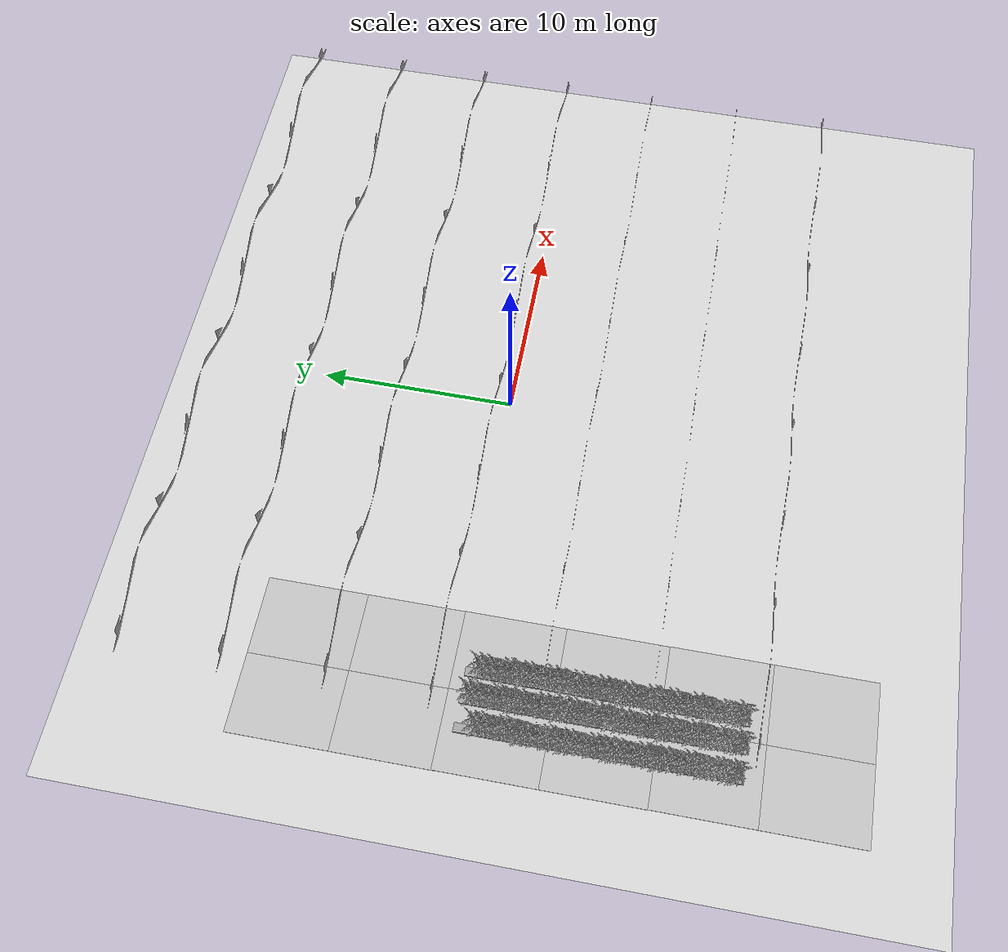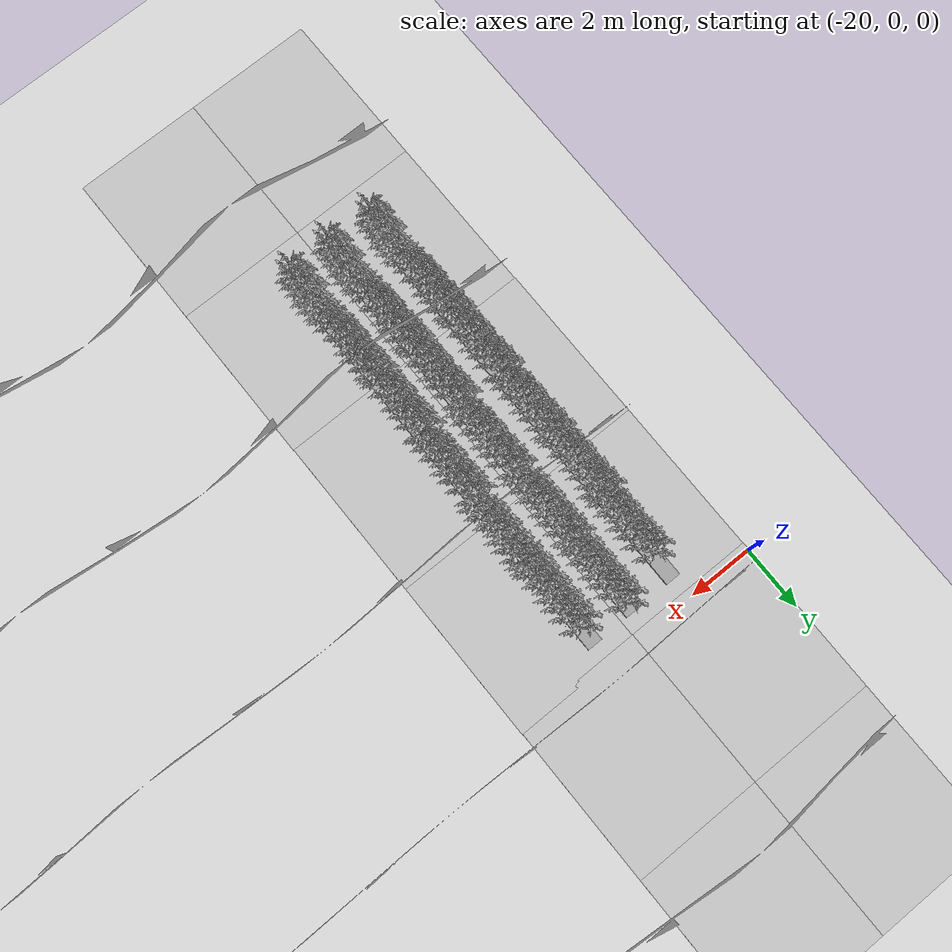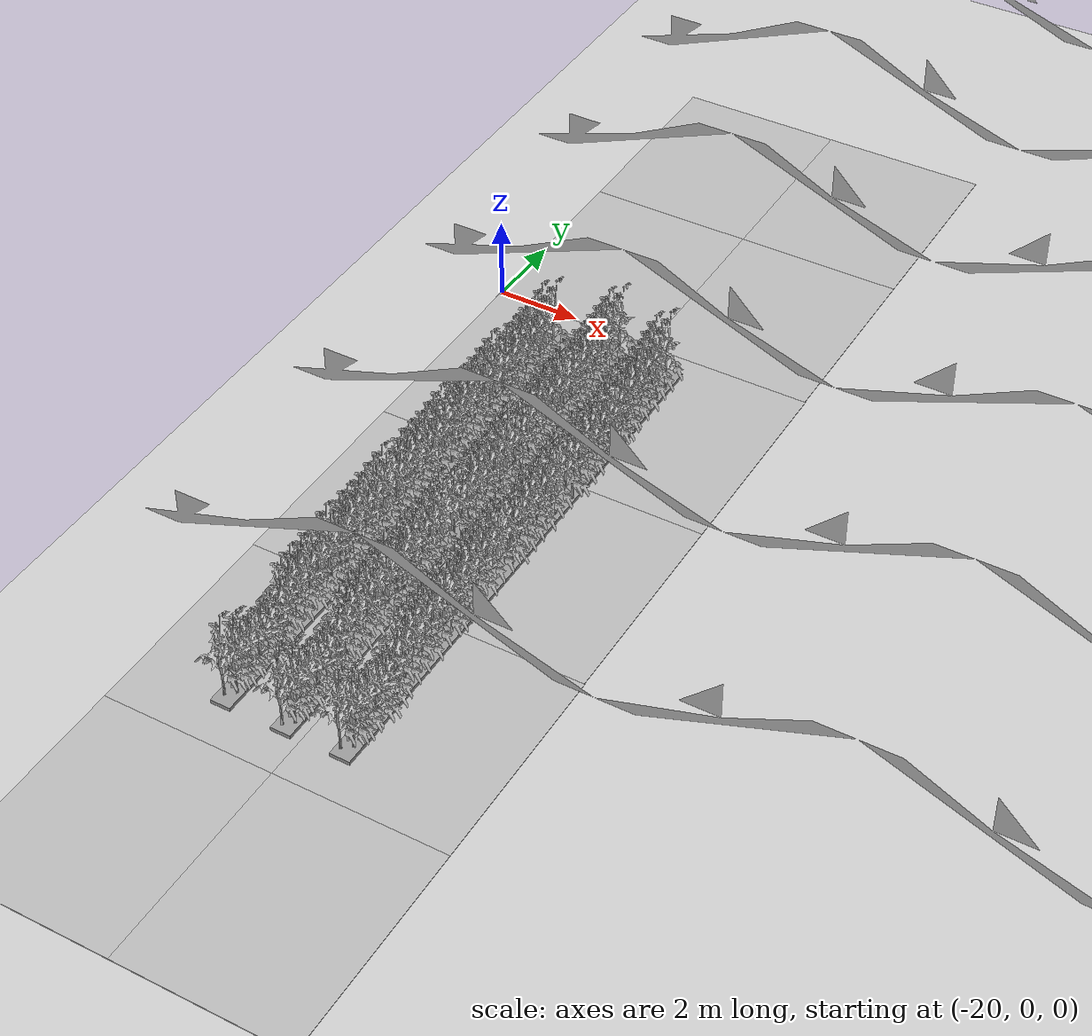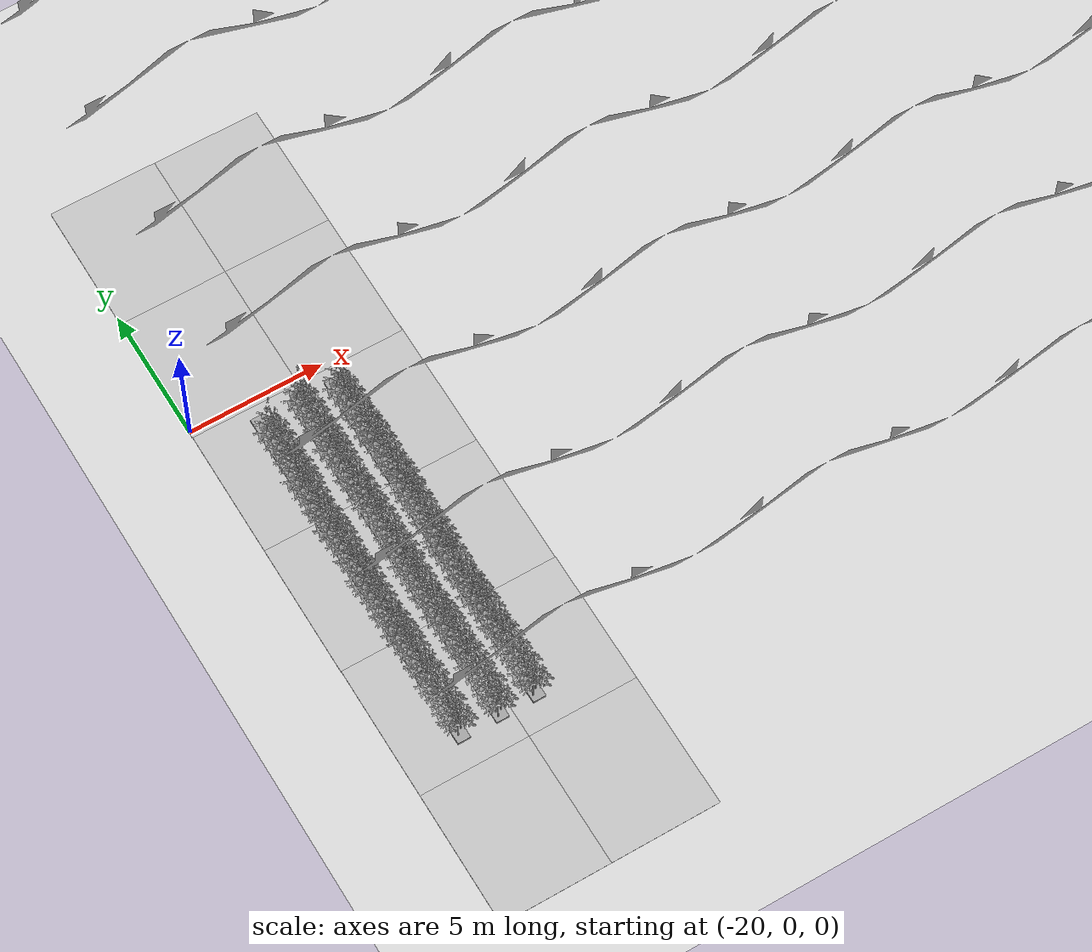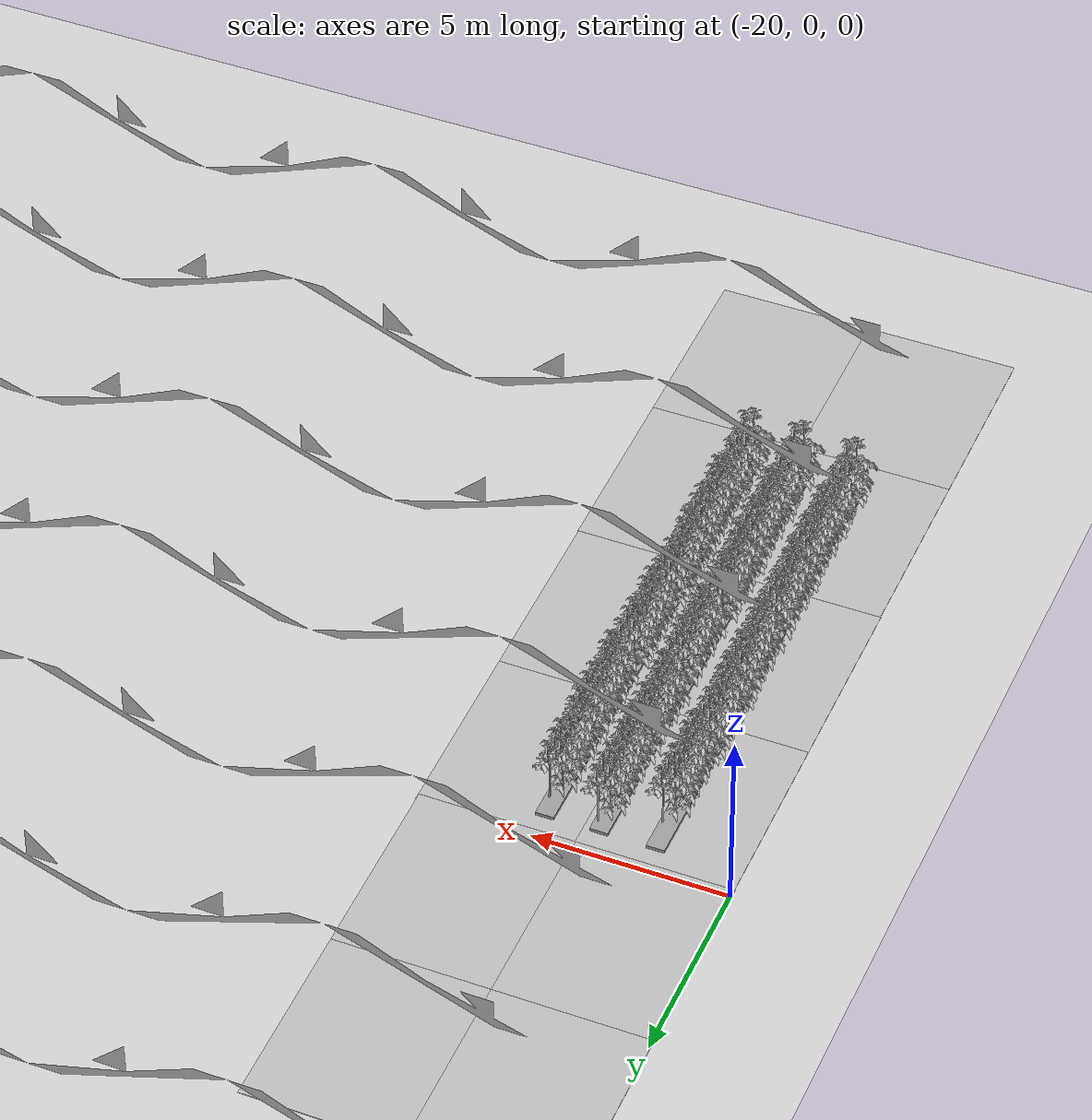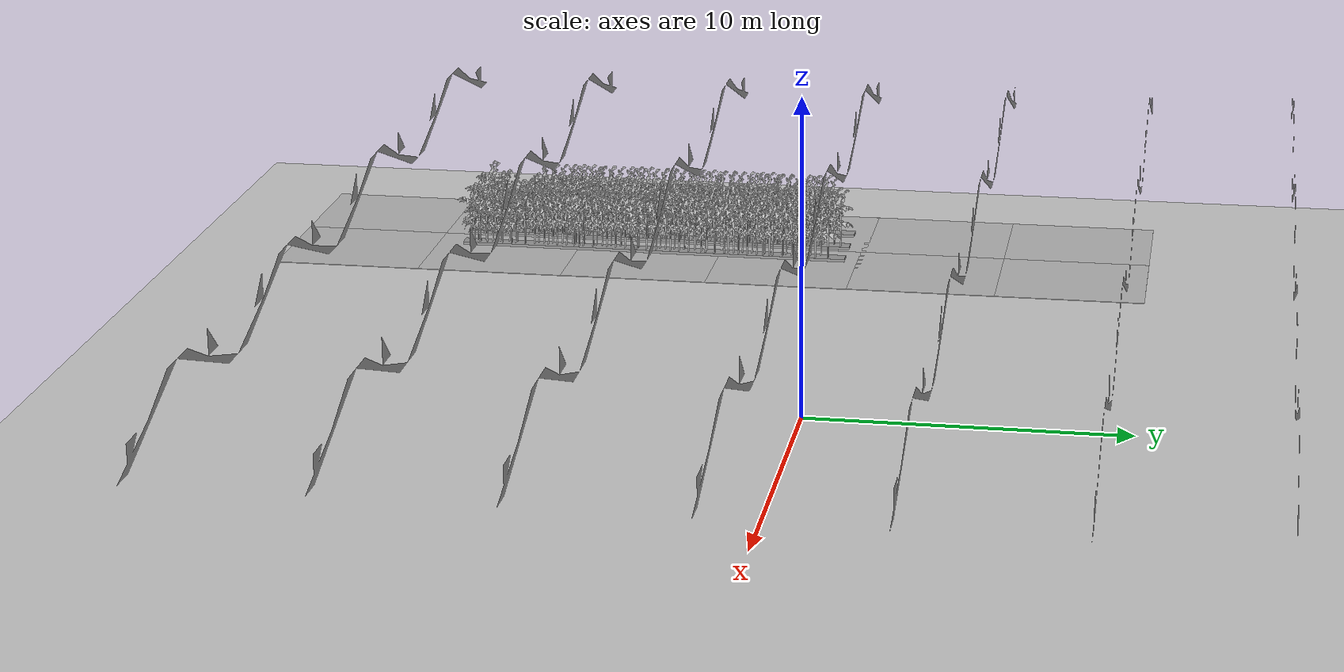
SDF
<sdf version="1.6">
 <world name="default">
  <light name="sun" type="directional">
   <pose>0 0 10 0 -0 0</pose>
   <diffuse>0.8 0.8 0.8 1</diffuse>
   <specular>0.2 0.2 0.2 1</specular>
   <attenuation>
    <range>1000</range>
    <constant>0.9</constant>
    <linear>0.01</linear>
    <quadratic>0.001</quadratic>
   </attenuation>
   <direction>-0.5 0.1 -0.9</direction>
  </light>
  <model name="ground_plane">
   <static>1</static>
   <link name="link">
    <collision name="collision">
     <geometry><plane><normal>0 0 1</normal><size>100 100</size></plane></geometry>
     <surface>
      <contact><collide_bitmask>65535</collide_bitmask></contact>
      <friction><ode><mu>100</mu><mu2>50</mu2></ode></friction>
     </surface>
    </collision>
    <visual name="visual">
     <cast_shadows>0</cast_shadows>
     <geometry><plane><normal>0 0 1</normal><size>100 100</size></plane></geometry>
     <material>
      <script><uri>file://media/materials/scripts/gazebo.material</uri><name>Gazebo/Grey</name></script>
     </material>
    </visual>
   </link>
  </model>
  <gravity>0 0 -9.8</gravity>
  <magnetic_field>6e-06 2.3e-05 -4.2e-05</magnetic_field>
  <atmosphere type="adiabatic"/>
  <physics name="default_physics" default="0" type="ode">
   <max_step_size>0.001</max_step_size>
   <real_time_factor>1</real_time_factor>
   <real_time_update_rate>1000</real_time_update_rate>
  </physics>
  <scene><ambient>0.4 0.4 0.4 1</ambient><background>0.7 0.7 0.7 1</background><shadows>1</shadows></scene>
  <audio><device>default</device></audio>
  <spherical_coordinates>
   <surface_model>EARTH_WGS84</surface_model>
   <latitude_deg>0</latitude_deg>
   <longitude_deg>0</longitude_deg>
   <elevation>0</elevation>
   <heading_deg>0</heading_deg>
  </spherical_coordinates>
  <model name="greenhouse">
   <static>1</static>
   <link name="link">
    <collision name="collision">
     <geometry>
      <mesh><scale>0.05 0.05 0.05</scale><uri>model://greenhouse/meshes/greenhouse.dae</uri></mesh>
     </geometry>
    </collision>
    <visual name="visual">
     <geometry>
      <mesh><scale>0.03 0.03 0.03</scale><uri>model://greenhouse/meshes/greenhouse.dae</uri></mesh>
     </geometry>
    </visual>
   </link>
   <pose>-24.6631 -23.579 0 0 -0 0</pose>
  </model>
  <model name="Middle_Plant_0">
   <model name="tomato_plant_big">
    <static>1</static>
    <link name="link">
     <collision name="collision">
      <geometry>
       <mesh><scale>5e-06 5e-06 6e-06</scale><uri>model://tomato_plant_big/meshes/tomato-plant.dae</uri></mesh>
      </geometry>
     </collision>
     <visual name="visual">
      <geometry>
       <mesh><scale>5e-06 5e-06 7e-06</scale><uri>model://tomato_plant_big/meshes/tomato-plant.dae</uri></mesh>
      </geometry>
     </visual>
    </link>
    <pose>0.085326 1.23023 0 0 -0 0</pose>
   </model>
   <model name="tomato_plant_big_0">
    <static>1</static>
    <link name="link">
     <collision name="collision">
      <geometry>
       <mesh><scale>5e-06 5e-06 6e-06</scale><uri>model://tomato_plant_big/meshes/tomato-plant.dae</uri></mesh>
      </geometry>
     </collision>
     <visual name="visual">
      <geometry>
       <mesh><scale>5e-06 5e-06 7e-06</scale><uri>model://tomato_plant_big/meshes/tomato-plant.dae</uri></mesh>
      </geometry>
     </visual>
    </link>
    <pose>-0.133881 0.970183 0 0 -0 0</pose>
   </model>
   <model name="tomato_plant_big_1">
    <static>1</static>
    <link name="link">
     <collision name="collision">
      <geometry>
       <mesh><scale>5e-06 5e-06 6e-06</scale><uri>model://tomato_plant_big/meshes/tomato-plant.dae</uri></mesh>
      </geometry>
     </collision>
     <visual name="visual">
      <geometry>
       <mesh><scale>5e-06 5e-06 7e-06</scale><uri>model://tomato_plant_big/meshes/tomato-plant.dae</uri></mesh>
      </geometry>
     </visual>
    </link>
    <pose>0.091162 0.792381 0 0 -0 0</pose>
   </model>
   <model name="tomato_plant_big_2">
    <static>1</static>
    <link name="link">
     <collision name="collision">
      <geometry>
       <mesh><scale>5e-06 5e-06 6e-06</scale><uri>model://tomato_plant_big/meshes/tomato-plant.dae</uri></mesh>
      </geometry>
     </collision>
     <visual name="visual">
      <geometry>
       <mesh><scale>5e-06 5e-06 7e-06</scale><uri>model://tomato_plant_big/meshes/tomato-plant.dae</uri></mesh>
      </geometry>
     </visual>
    </link>
    <pose>-0.099228 0.602587 0 0 -0 0</pose>
   </model>
   <model name="tomato_plant_big_3">
    <static>1</static>
    <link name="link">
     <collision name="collision">
      <geometry>
       <mesh><scale>5e-06 5e-06 6e-06</scale><uri>model://tomato_plant_big/meshes/tomato-plant.dae</uri></mesh>
      </geometry>
     </collision>
     <visual name="visual">
      <geometry>
       <mesh><scale>5e-06 5e-06 7e-06</scale><uri>model://tomato_plant_big/meshes/tomato-plant.dae</uri></mesh>
      </geometry>
     </visual>
    </link>
    <pose>0.083199 0.447645 0 0 -0 0</pose>
   </model>
   <model name="tomato_plant_big_4">
    <static>1</static>
    <link name="link">
     <collision name="collision">
      <geometry>
       <mesh><scale>5e-06 5e-06 6e-06</scale><uri>model://tomato_plant_big/meshes/tomato-plant.dae</uri></mesh>
      </geometry>
     </collision>
     <visual name="visual">
      <geometry>
       <mesh><scale>5e-06 5e-06 7e-06</scale><uri>model://tomato_plant_big/meshes/tomato-plant.dae</uri></mesh>
      </geometry>
     </visual>
    </link>
    <pose>-0.079499 0.263486 0 0 -0 0</pose>
   </model>
   <model name="tomato_plant_big_5">
    <static>1</static>
    <link name="link">
     <collision name="collision">
      <geometry>
       <mesh><scale>5e-06 5e-06 6e-06</scale><uri>model://tomato_plant_big/meshes/tomato-plant.dae</uri></mesh>
      </geometry>
     </collision>
     <visual name="visual">
      <geometry>
       <mesh><scale>5e-06 5e-06 7e-06</scale><uri>model://tomato_plant_big/meshes/tomato-plant.dae</uri></mesh>
      </geometry>
     </visual>
    </link>
    <pose>-0.033274 -0.040578 0 0 -0 0</pose>
   </model>
   <model name="tomato_plant_big_6">
    <static>1</static>
    <link name="link">
     <collision name="collision">
      <geometry>
       <mesh><scale>5e-06 5e-06 6e-06</scale><uri>model://tomato_plant_big/meshes/tomato-plant.dae</uri></mesh>
      </geometry>
     </collision>
     <visual name="visual">
      <geometry>
       <mesh><scale>5e-06 5e-06 7e-06</scale><uri>model://tomato_plant_big/meshes/tomato-plant.dae</uri></mesh>
      </geometry>
     </visual>
    </link>
    <pose>-0.07669 -0.382406 0 0 -0 0</pose>
   </model>
   <model name="tomato_plant_big_7">
    <static>1</static>
    <link name="link">
     <collision name="collision">
      <geometry>
       <mesh><scale>5e-06 5e-06 6e-06</scale><uri>model://tomato_plant_big/meshes/tomato-plant.dae</uri></mesh>
      </geometry>
     </collision>
     <visual name="visual">
      <geometry>
       <mesh><scale>5e-06 5e-06 7e-06</scale><uri>model://tomato_plant_big/meshes/tomato-plant.dae</uri></mesh>
      </geometry>
     </visual>
    </link>
    <pose>0.092388 -0.348189 0 0 -0 0</pose>
   </model>
   <model name="tomato_plant_big_8">
    <static>1</static>
    <link name="link">
     <collision name="collision">
      <geometry>
       <mesh><scale>5e-06 5e-06 6e-06</scale><uri>model://tomato_plant_big/meshes/tomato-plant.dae</uri></mesh>
      </geometry>
     </collision>
     <visual name="visual">
      <geometry>
       <mesh><scale>5e-06 5e-06 7e-06</scale><uri>model://tomato_plant_big/meshes/tomato-plant.dae</uri></mesh>
      </geometry>
     </visual>
    </link>
    <pose>0.099522 -0.697525 0 0 -0 0</pose>
   </model>
   <model name="tomato_plant_big_9">
    <static>1</static>
    <link name="link">
     <collision name="collision">
      <geometry>
       <mesh><scale>5e-06 5e-06 6e-06</scale><uri>model://tomato_plant_big/meshes/tomato-plant.dae</uri></mesh>
      </geometry>
     </collision>
     <visual name="visual">
      <geometry>
       <mesh><scale>5e-06 5e-06 7e-06</scale><uri>model://tomato_plant_big/meshes/tomato-plant.dae</uri></mesh>
      </geometry>
     </visual>
    </link>
    <pose>-0.050449 -0.712772 0 0 -0 0</pose>
   </model>
   <model name="tomato_plant_medium">
    <static>1</static>
    <link name="link">
     <collision name="collision">
      <geometry>
       <mesh><scale>5e-06 5e-06 6e-06</scale><uri>model://tomato_plant_medium/meshes/tomato-plant.dae</uri></mesh>
      </geometry>
     </collision>
     <visual name="visual">
      <geometry>
       <mesh><scale>5e-06 5e-06 6e-06</scale><uri>model://tomato_plant_medium/meshes/tomato-plant.dae</uri></mesh>
      </geometry>
     </visual>
    </link>
    <pose>0.078434 0.139842 0 0 -0 0</pose>
   </model>
   <model name="tomato_plant_medium_0">
    <static>1</static>
    <link name="link">
     <collision name="collision">
      <geometry>
       <mesh><scale>5e-06 5e-06 6e-06</scale><uri>model://tomato_plant_medium/meshes/tomato-plant.dae</uri></mesh>
      </geometry>
     </collision>
     <visual name="visual">
      <geometry>
       <mesh><scale>5e-06 5e-06 6e-06</scale><uri>model://tomato_plant_medium/meshes/tomato-plant.dae</uri></mesh>
      </geometry>
     </visual>
    </link>
    <pose>-0.079755 -0.244483 0 0 -0 0</pose>
   </model>
   <model name="tomato_plant_medium_1">
    <static>1</static>
    <link name="link">
     <collision name="collision">
      <geometry>
       <mesh><scale>5e-06 5e-06 6e-06</scale><uri>model://tomato_plant_medium/meshes/tomato-plant.dae</uri></mesh>
      </geometry>
     </collision>
     <visual name="visual">
      <geometry>
       <mesh><scale>5e-06 5e-06 6e-06</scale><uri>model://tomato_plant_medium/meshes/tomato-plant.dae</uri></mesh>
      </geometry>
     </visual>
    </link>
    <pose>0.106744 -1.01815 0 0 -0 0</pose>
   </model>
   <model name="tomato_plant_small">
    <static>1</static>
    <link name="link">
     <collision name="collision">
      <geometry>
       <mesh><scale>5e-06 5e-06 5e-06</scale><uri>model://tomato_plant_small/meshes/tomato-plant.dae</uri></mesh>
      </geometry>
     </collision>
     <visual name="visual">
      <geometry>
       <mesh><scale>5e-06 5e-06 5e-06</scale><uri>model://tomato_plant_small/meshes/tomato-plant.dae</uri></mesh>
      </geometry>
     </visual>
    </link>
    <pose>-0.083979 -1.00222 0 0 -0 0</pose>
   </model>
   <static>0</static>
   <pose>-17.8416 -6.93507 0 0 -0 0</pose>
  </model>
  <model name="Middle_Plant_1">
   <model name="tomato_plant_big">
    <static>1</static>
    <link name="link">
     <collision name="collision">
      <geometry>
       <mesh><scale>5e-06 5e-06 6e-06</scale><uri>model://tomato_plant_big/meshes/tomato-plant.dae</uri></mesh>
      </geometry>
     </collision>
     <visual name="visual">
      <geometry>
       <mesh><scale>5e-06 5e-06 7e-06</scale><uri>model://tomato_plant_big/meshes/tomato-plant.dae</uri></mesh>
      </geometry>
     </visual>
    </link>
    <pose>0.085326 1.23023 0 0 -0 0</pose>
   </model>
   <model name="tomato_plant_big_0">
    <static>1</static>
    <link name="link">
     <collision name="collision">
      <geometry>
       <mesh><scale>5e-06 5e-06 6e-06</scale><uri>model://tomato_plant_big/meshes/tomato-plant.dae</uri></mesh>
      </geometry>
     </collision>
     <visual name="visual">
      <geometry>
       <mesh><scale>5e-06 5e-06 7e-06</scale><uri>model://tomato_plant_big/meshes/tomato-plant.dae</uri></mesh>
      </geometry>
     </visual>
    </link>
    <pose>-0.133881 0.970183 0 0 -0 0</pose>
   </model>
   <model name="tomato_plant_big_1">
    <static>1</static>
    <link name="link">
     <collision name="collision">
      <geometry>
       <mesh><scale>5e-06 5e-06 6e-06</scale><uri>model://tomato_plant_big/meshes/tomato-plant.dae</uri></mesh>
      </geometry>
     </collision>
     <visual name="visual">
      <geometry>
       <mesh><scale>5e-06 5e-06 7e-06</scale><uri>model://tomato_plant_big/meshes/tomato-plant.dae</uri></mesh>
      </geometry>
     </visual>
    </link>
    <pose>0.091162 0.792381 0 0 -0 0</pose>
   </model>
   <model name="tomato_plant_big_2">
    <static>1</static>
    <link name="link">
     <collision name="collision">
      <geometry>
       <mesh><scale>5e-06 5e-06 6e-06</scale><uri>model://tomato_plant_big/meshes/tomato-plant.dae</uri></mesh>
      </geometry>
     </collision>
     <visual name="visual">
      <geometry>
       <mesh><scale>5e-06 5e-06 7e-06</scale><uri>model://tomato_plant_big/meshes/tomato-plant.dae</uri></mesh>
      </geometry>
     </visual>
    </link>
    <pose>-0.099228 0.602587 0 0 -0 0</pose>
   </model>
   <model name="tomato_plant_big_3">
    <static>1</static>
    <link name="link">
     <collision name="collision">
      <geometry>
       <mesh><scale>5e-06 5e-06 6e-06</scale><uri>model://tomato_plant_big/meshes/tomato-plant.dae</uri></mesh>
      </geometry>
     </collision>
     <visual name="visual">
      <geometry>
       <mesh><scale>5e-06 5e-06 7e-06</scale><uri>model://tomato_plant_big/meshes/tomato-plant.dae</uri></mesh>
      </geometry>
     </visual>
    </link>
    <pose>0.083199 0.447645 0 0 -0 0</pose>
   </model>
   <model name="tomato_plant_big_4">
    <static>1</static>
    <link name="link">
     <collision name="collision">
      <geometry>
       <mesh><scale>5e-06 5e-06 6e-06</scale><uri>model://tomato_plant_big/meshes/tomato-plant.dae</uri></mesh>
      </geometry>
     </collision>
     <visual name="visual">
      <geometry>
       <mesh><scale>5e-06 5e-06 7e-06</scale><uri>model://tomato_plant_big/meshes/tomato-plant.dae</uri></mesh>
      </geometry>
     </visual>
    </link>
    <pose>-0.079499 0.263486 0 0 -0 0</pose>
   </model>
   <model name="tomato_plant_big_5">
    <static>1</static>
    <link name="link">
     <collision name="collision">
      <geometry>
       <mesh><scale>5e-06 5e-06 6e-06</scale><uri>model://tomato_plant_big/meshes/tomato-plant.dae</uri></mesh>
      </geometry>
     </collision>
     <visual name="visual">
      <geometry>
       <mesh><scale>5e-06 5e-06 7e-06</scale><uri>model://tomato_plant_big/meshes/tomato-plant.dae</uri></mesh>
      </geometry>
     </visual>
    </link>
    <pose>-0.033274 -0.040578 0 0 -0 0</pose>
   </model>
   <model name="tomato_plant_big_6">
    <static>1</static>
    <link name="link">
     <collision name="collision">
      <geometry>
       <mesh><scale>5e-06 5e-06 6e-06</scale><uri>model://tomato_plant_big/meshes/tomato-plant.dae</uri></mesh>
      </geometry>
     </collision>
     <visual name="visual">
      <geometry>
       <mesh><scale>5e-06 5e-06 7e-06</scale><uri>model://tomato_plant_big/meshes/tomato-plant.dae</uri></mesh>
      </geometry>
     </visual>
    </link>
    <pose>-0.07669 -0.382406 0 0 -0 0</pose>
   </model>
   <model name="tomato_plant_big_7">
    <static>1</static>
    <link name="link">
     <collision name="collision">
      <geometry>
       <mesh><scale>5e-06 5e-06 6e-06</scale><uri>model://tomato_plant_big/meshes/tomato-plant.dae</uri></mesh>
      </geometry>
     </collision>
     <visual name="visual">
      <geometry>
       <mesh><scale>5e-06 5e-06 7e-06</scale><uri>model://tomato_plant_big/meshes/tomato-plant.dae</uri></mesh>
      </geometry>
     </visual>
    </link>
    <pose>0.092388 -0.348189 0 0 -0 0</pose>
   </model>
   <model name="tomato_plant_big_8">
    <static>1</static>
    <link name="link">
     <collision name="collision">
      <geometry>
       <mesh><scale>5e-06 5e-06 6e-06</scale><uri>model://tomato_plant_big/meshes/tomato-plant.dae</uri></mesh>
      </geometry>
     </collision>
     <visual name="visual">
      <geometry>
       <mesh><scale>5e-06 5e-06 7e-06</scale><uri>model://tomato_plant_big/meshes/tomato-plant.dae</uri></mesh>
      </geometry>
     </visual>
    </link>
    <pose>0.099522 -0.697525 0 0 -0 0</pose>
   </model>
   <model name="tomato_plant_big_9">
    <static>1</static>
    <link name="link">
     <collision name="collision">
      <geometry>
       <mesh><scale>5e-06 5e-06 6e-06</scale><uri>model://tomato_plant_big/meshes/tomato-plant.dae</uri></mesh>
      </geometry>
     </collision>
     <visual name="visual">
      <geometry>
       <mesh><scale>5e-06 5e-06 7e-06</scale><uri>model://tomato_plant_big/meshes/tomato-plant.dae</uri></mesh>
      </geometry>
     </visual>
    </link>
    <pose>-0.050449 -0.712772 0 0 -0 0</pose>
   </model>
   <model name="tomato_plant_medium">
    <static>1</static>
    <link name="link">
     <collision name="collision">
      <geometry>
       <mesh><scale>5e-06 5e-06 6e-06</scale><uri>model://tomato_plant_medium/meshes/tomato-plant.dae</uri></mesh>
      </geometry>
     </collision>
     <visual name="visual">
      <geometry>
       <mesh><scale>5e-06 5e-06 6e-06</scale><uri>model://tomato_plant_medium/meshes/tomato-plant.dae</uri></mesh>
      </geometry>
     </visual>
    </link>
    <pose>0.078434 0.139842 0 0 -0 0</pose>
   </model>
   <model name="tomato_plant_medium_0">
    <static>1</static>
    <link name="link">
     <collision name="collision">
      <geometry>
       <mesh><scale>5e-06 5e-06 6e-06</scale><uri>model://tomato_plant_medium/meshes/tomato-plant.dae</uri></mesh>
      </geometry>
     </collision>
     <visual name="visual">
      <geometry>
       <mesh><scale>5e-06 5e-06 6e-06</scale><uri>model://tomato_plant_medium/meshes/tomato-plant.dae</uri></mesh>
      </geometry>
     </visual>
    </link>
    <pose>-0.079755 -0.244483 0 0 -0 0</pose>
   </model>
   <model name="tomato_plant_medium_1">
    <static>1</static>
    <link name="link">
     <collision name="collision">
      <geometry>
       <mesh><scale>5e-06 5e-06 6e-06</scale><uri>model://tomato_plant_medium/meshes/tomato-plant.dae</uri></mesh>
      </geometry>
     </collision>
     <visual name="visual">
      <geometry>
       <mesh><scale>5e-06 5e-06 6e-06</scale><uri>model://tomato_plant_medium/meshes/tomato-plant.dae</uri></mesh>
      </geometry>
     </visual>
    </link>
    <pose>0.106744 -1.01815 0 0 -0 0</pose>
   </model>
   <model name="tomato_plant_small">
    <static>1</static>
    <link name="link">
     <collision name="collision">
      <geometry>
       <mesh><scale>5e-06 5e-06 5e-06</scale><uri>model://tomato_plant_small/meshes/tomato-plant.dae</uri></mesh>
      </geometry>
     </collision>
     <visual name="visual">
      <geometry>
       <mesh><scale>5e-06 5e-06 5e-06</scale><uri>model://tomato_plant_small/meshes/tomato-plant.dae</uri></mesh>
      </geometry>
     </visual>
    </link>
    <pose>-0.083979 -1.00222 0 0 -0 0</pose>
   </model>
   <static>0</static>
   <pose>-17.8578 -4.83213 0 0 -0 0</pose>
  </model>
  <model name="Middle_Plant_2">
   <model name="tomato_plant_big">
    <static>1</static>
    <link name="link">
     <collision name="collision">
      <geometry>
       <mesh><scale>5e-06 5e-06 6e-06</scale><uri>model://tomato_plant_big/meshes/tomato-plant.dae</uri></mesh>
      </geometry>
     </collision>
     <visual name="visual">
      <geometry>
       <mesh><scale>5e-06 5e-06 7e-06</scale><uri>model://tomato_plant_big/meshes/tomato-plant.dae</uri></mesh>
      </geometry>
     </visual>
    </link>
    <pose>0.085326 1.23023 0 0 -0 0</pose>
   </model>
   <model name="tomato_plant_big_0">
    <static>1</static>
    <link name="link">
     <collision name="collision">
      <geometry>
       <mesh><scale>5e-06 5e-06 6e-06</scale><uri>model://tomato_plant_big/meshes/tomato-plant.dae</uri></mesh>
      </geometry>
     </collision>
     <visual name="visual">
      <geometry>
       <mesh><scale>5e-06 5e-06 7e-06</scale><uri>model://tomato_plant_big/meshes/tomato-plant.dae</uri></mesh>
      </geometry>
     </visual>
    </link>
    <pose>-0.133881 0.970183 0 0 -0 0</pose>
   </model>
   <model name="tomato_plant_big_1">
    <static>1</static>
    <link name="link">
     <collision name="collision">
      <geometry>
       <mesh><scale>5e-06 5e-06 6e-06</scale><uri>model://tomato_plant_big/meshes/tomato-plant.dae</uri></mesh>
      </geometry>
     </collision>
     <visual name="visual">
      <geometry>
       <mesh><scale>5e-06 5e-06 7e-06</scale><uri>model://tomato_plant_big/meshes/tomato-plant.dae</uri></mesh>
      </geometry>
     </visual>
    </link>
    <pose>0.091162 0.792381 0 0 -0 0</pose>
   </model>
   <model name="tomato_plant_big_2">
    <static>1</static>
    <link name="link">
     <collision name="collision">
      <geometry>
       <mesh><scale>5e-06 5e-06 6e-06</scale><uri>model://tomato_plant_big/meshes/tomato-plant.dae</uri></mesh>
      </geometry>
     </collision>
     <visual name="visual">
      <geometry>
       <mesh><scale>5e-06 5e-06 7e-06</scale><uri>model://tomato_plant_big/meshes/tomato-plant.dae</uri></mesh>
      </geometry>
     </visual>
    </link>
    <pose>-0.099228 0.602587 0 0 -0 0</pose>
   </model>
   <model name="tomato_plant_big_3">
    <static>1</static>
    <link name="link">
     <collision name="collision">
      <geometry>
       <mesh><scale>5e-06 5e-06 6e-06</scale><uri>model://tomato_plant_big/meshes/tomato-plant.dae</uri></mesh>
      </geometry>
     </collision>
     <visual name="visual">
      <geometry>
       <mesh><scale>5e-06 5e-06 7e-06</scale><uri>model://tomato_plant_big/meshes/tomato-plant.dae</uri></mesh>
      </geometry>
     </visual>
    </link>
    <pose>0.083199 0.447645 0 0 -0 0</pose>
   </model>
   <model name="tomato_plant_big_4">
    <static>1</static>
    <link name="link">
     <collision name="collision">
      <geometry>
       <mesh><scale>5e-06 5e-06 6e-06</scale><uri>model://tomato_plant_big/meshes/tomato-plant.dae</uri></mesh>
      </geometry>
     </collision>
     <visual name="visual">
      <geometry>
       <mesh><scale>5e-06 5e-06 7e-06</scale><uri>model://tomato_plant_big/meshes/tomato-plant.dae</uri></mesh>
      </geometry>
     </visual>
    </link>
    <pose>-0.079499 0.263486 0 0 -0 0</pose>
   </model>
   <model name="tomato_plant_big_5">
    <static>1</static>
    <link name="link">
     <collision name="collision">
      <geometry>
       <mesh><scale>5e-06 5e-06 6e-06</scale><uri>model://tomato_plant_big/meshes/tomato-plant.dae</uri></mesh>
      </geometry>
     </collision>
     <visual name="visual">
      <geometry>
       <mesh><scale>5e-06 5e-06 7e-06</scale><uri>model://tomato_plant_big/meshes/tomato-plant.dae</uri></mesh>
      </geometry>
     </visual>
    </link>
    <pose>-0.033274 -0.040578 0 0 -0 0</pose>
   </model>
   <model name="tomato_plant_big_6">
    <static>1</static>
    <link name="link">
     <collision name="collision">
      <geometry>
       <mesh><scale>5e-06 5e-06 6e-06</scale><uri>model://tomato_plant_big/meshes/tomato-plant.dae</uri></mesh>
      </geometry>
     </collision>
     <visual name="visual">
      <geometry>
       <mesh><scale>5e-06 5e-06 7e-06</scale><uri>model://tomato_plant_big/meshes/tomato-plant.dae</uri></mesh>
      </geometry>
     </visual>
    </link>
    <pose>-0.07669 -0.382406 0 0 -0 0</pose>
   </model>
   <model name="tomato_plant_big_7">
    <static>1</static>
    <link name="link">
     <collision name="collision">
      <geometry>
       <mesh><scale>5e-06 5e-06 6e-06</scale><uri>model://tomato_plant_big/meshes/tomato-plant.dae</uri></mesh>
      </geometry>
     </collision>
     <visual name="visual">
      <geometry>
       <mesh><scale>5e-06 5e-06 7e-06</scale><uri>model://tomato_plant_big/meshes/tomato-plant.dae</uri></mesh>
      </geometry>
     </visual>
    </link>
    <pose>0.092388 -0.348189 0 0 -0 0</pose>
   </model>
   <model name="tomato_plant_big_8">
    <static>1</static>
    <link name="link">
     <collision name="collision">
      <geometry>
       <mesh><scale>5e-06 5e-06 6e-06</scale><uri>model://tomato_plant_big/meshes/tomato-plant.dae</uri></mesh>
      </geometry>
     </collision>
     <visual name="visual">
      <geometry>
       <mesh><scale>5e-06 5e-06 7e-06</scale><uri>model://tomato_plant_big/meshes/tomato-plant.dae</uri></mesh>
      </geometry>
     </visual>
    </link>
    <pose>0.099522 -0.697525 0 0 -0 0</pose>
   </model>
   <model name="tomato_plant_big_9">
    <static>1</static>
    <link name="link">
     <collision name="collision">
      <geometry>
       <mesh><scale>5e-06 5e-06 6e-06</scale><uri>model://tomato_plant_big/meshes/tomato-plant.dae</uri></mesh>
      </geometry>
     </collision>
     <visual name="visual">
      <geometry>
       <mesh><scale>5e-06 5e-06 7e-06</scale><uri>model://tomato_plant_big/meshes/tomato-plant.dae</uri></mesh>
      </geometry>
     </visual>
    </link>
    <pose>-0.050449 -0.712772 0 0 -0 0</pose>
   </model>
   <model name="tomato_plant_medium">
    <static>1</static>
    <link name="link">
     <collision name="collision">
      <geometry>
       <mesh><scale>5e-06 5e-06 6e-06</scale><uri>model://tomato_plant_medium/meshes/tomato-plant.dae</uri></mesh>
      </geometry>
     </collision>
     <visual name="visual">
      <geometry>
       <mesh><scale>5e-06 5e-06 6e-06</scale><uri>model://tomato_plant_medium/meshes/tomato-plant.dae</uri></mesh>
      </geometry>
     </visual>
    </link>
    <pose>0.078434 0.139842 0 0 -0 0</pose>
   </model>
   <model name="tomato_plant_medium_0">
    <static>1</static>
    <link name="link">
     <collision name="collision">
      <geometry>
       <mesh><scale>5e-06 5e-06 6e-06</scale><uri>model://tomato_plant_medium/meshes/tomato-plant.dae</uri></mesh>
      </geometry>
     </collision>
     <visual name="visual">
      <geometry>
       <mesh><scale>5e-06 5e-06 6e-06</scale><uri>model://tomato_plant_medium/meshes/tomato-plant.dae</uri></mesh>
      </geometry>
     </visual>
    </link>
    <pose>-0.079755 -0.244483 0 0 -0 0</pose>
   </model>
   <model name="tomato_plant_medium_1">
    <static>1</static>
    <link name="link">
     <collision name="collision">
      <geometry>
       <mesh><scale>5e-06 5e-06 6e-06</scale><uri>model://tomato_plant_medium/meshes/tomato-plant.dae</uri></mesh>
      </geometry>
     </collision>
     <visual name="visual">
      <geometry>
       <mesh><scale>5e-06 5e-06 6e-06</scale><uri>model://tomato_plant_medium/meshes/tomato-plant.dae</uri></mesh>
      </geometry>
     </visual>
    </link>
    <pose>0.106744 -1.01815 0 0 -0 0</pose>
   </model>
   <model name="tomato_plant_small">
    <static>1</static>
    <link name="link">
     <collision name="collision">
      <geometry>
       <mesh><scale>5e-06 5e-06 5e-06</scale><uri>model://tomato_plant_small/meshes/tomato-plant.dae</uri></mesh>
      </geometry>
     </collision>
     <visual name="visual">
      <geometry>
       <mesh><scale>5e-06 5e-06 5e-06</scale><uri>model://tomato_plant_small/meshes/tomato-plant.dae</uri></mesh>
      </geometry>
     </visual>
    </link>
    <pose>-0.083979 -1.00222 0 0 -0 0</pose>
   </model>
   <static>0</static>
   <pose>-17.7846 -2.78008 0 0 -0 0</pose>
  </model>
  <model name="Front_Plant">
   <model name="Front_Plant">
    <model name="Front_Plant">
     <model name="tomato_plant_big">
      <static>1</static>
      <link name="link">
       <collision name="collision">
        <geometry>
         <mesh><scale>5e-06 5e-06 6e-06</scale><uri>model://tomato_plant_big/meshes/tomato-plant.dae</uri></mesh>
        </geometry>
       </collision>
       <visual name="visual">
        <geometry>
         <mesh><scale>5e-06 5e-06 7e-06</scale><uri>model://tomato_plant_big/meshes/tomato-plant.dae</uri></mesh>
        </geometry>
       </visual>
      </link>
      <pose>0.066099 -0.5693 0 0 -0 0</pose>
     </model>
     <model name="tomato_plant_big_0">
      <static>1</static>
      <link name="link">
       <collision name="collision">
        <geometry>
         <mesh><scale>5e-06 5e-06 6e-06</scale><uri>model://tomato_plant_big/meshes/tomato-plant.dae</uri></mesh>
        </geometry>
       </collision>
       <visual name="visual">
        <geometry>
         <mesh><scale>5e-06 5e-06 7e-06</scale><uri>model://tomato_plant_big/meshes/tomato-plant.dae</uri></mesh>
        </geometry>
       </visual>
      </link>
      <pose>-0.127857 -0.732187 0 0 -0 0</pose>
     </model>
     <model name="tomato_plant_medium">
      <static>1</static>
      <link name="link">
       <collision name="collision">
        <geometry>
         <mesh><scale>5e-06 5e-06 6e-06</scale><uri>model://tomato_plant_medium/meshes/tomato-plant.dae</uri></mesh>
        </geometry>
       </collision>
       <visual name="visual">
        <geometry>
         <mesh><scale>5e-06 5e-06 6e-06</scale><uri>model://tomato_plant_medium/meshes/tomato-plant.dae</uri></mesh>
        </geometry>
       </visual>
      </link>
      <pose>0.122987 0.218142 0 0 -0 0</pose>
     </model>
     <model name="tomato_plant_medium_0">
      <static>1</static>
      <link name="link">
       <collision name="collision">
        <geometry>
         <mesh><scale>5e-06 5e-06 6e-06</scale><uri>model://tomato_plant_medium/meshes/tomato-plant.dae</uri></mesh>
        </geometry>
       </collision>
       <visual name="visual">
        <geometry>
         <mesh><scale>5e-06 5e-06 6e-06</scale><uri>model://tomato_plant_medium/meshes/tomato-plant.dae</uri></mesh>
        </geometry>
       </visual>
      </link>
      <pose>0.063601 -0.11224 0 0 -0 0</pose>
     </model>
     <model name="tomato_plant_medium_1">
      <static>1</static>
      <link name="link">
       <collision name="collision">
        <geometry>
         <mesh><scale>5e-06 5e-06 6e-06</scale><uri>model://tomato_plant_medium/meshes/tomato-plant.dae</uri></mesh>
        </geometry>
       </collision>
       <visual name="visual">
        <geometry>
         <mesh><scale>5e-06 5e-06 6e-06</scale><uri>model://tomato_plant_medium/meshes/tomato-plant.dae</uri></mesh>
        </geometry>
       </visual>
      </link>
      <pose>-0.136409 -0.201165 0 0 -0 0</pose>
     </model>
     <model name="tomato_plant_medium_2">
      <static>1</static>
      <link name="link">
       <collision name="collision">
        <geometry>
         <mesh><scale>5e-06 5e-06 6e-06</scale><uri>model://tomato_plant_medium/meshes/tomato-plant.dae</uri></mesh>
        </geometry>
       </collision>
       <visual name="visual">
        <geometry>
         <mesh><scale>5e-06 5e-06 6e-06</scale><uri>model://tomato_plant_medium/meshes/tomato-plant.dae</uri></mesh>
        </geometry>
       </visual>
      </link>
      <pose>0.058749 -0.366518 0 0 -0 0</pose>
     </model>
     <model name="tomato_plant_small">
      <static>1</static>
      <link name="link">
       <collision name="collision">
        <geometry>
         <mesh><scale>5e-06 5e-06 5e-06</scale><uri>model://tomato_plant_small/meshes/tomato-plant.dae</uri></mesh>
        </geometry>
       </collision>
       <visual name="visual">
        <geometry>
         <mesh><scale>5e-06 5e-06 5e-06</scale><uri>model://tomato_plant_small/meshes/tomato-plant.dae</uri></mesh>
        </geometry>
       </visual>
      </link>
      <pose>-0.070714 0.646602 0 0 -0 0</pose>
     </model>
     <model name="tomato_plant_small_0">
      <static>1</static>
      <link name="link">
       <collision name="collision">
        <geometry>
         <mesh><scale>5e-06 5e-06 5e-06</scale><uri>model://tomato_plant_small/meshes/tomato-plant.dae</uri></mesh>
        </geometry>
       </collision>
       <visual name="visual">
        <geometry>
         <mesh><scale>5e-06 5e-06 5e-06</scale><uri>model://tomato_plant_small/meshes/tomato-plant.dae</uri></mesh>
        </geometry>
       </visual>
      </link>
      <pose>0.074729 0.75209 0 0 -0 0</pose>
     </model>
     <model name="tomato_plant_small_1">
      <static>1</static>
      <link name="link">
       <collision name="collision">
        <geometry>
         <mesh><scale>5e-06 5e-06 5e-06</scale><uri>model://tomato_plant_small/meshes/tomato-plant.dae</uri></mesh>
        </geometry>
       </collision>
       <visual name="visual">
        <geometry>
         <mesh><scale>5e-06 5e-06 5e-06</scale><uri>model://tomato_plant_small/meshes/tomato-plant.dae</uri></mesh>
        </geometry>
       </visual>
      </link>
      <pose>0.12147 0.444739 0 0 -0 0</pose>
     </model>
     <model name="tomato_plant_small_2">
      <static>1</static>
      <link name="link">
       <collision name="collision">
        <geometry>
         <mesh><scale>5e-06 5e-06 5e-06</scale><uri>model://tomato_plant_small/meshes/tomato-plant.dae</uri></mesh>
        </geometry>
       </collision>
       <visual name="visual">
        <geometry>
         <mesh><scale>5e-06 5e-06 5e-06</scale><uri>model://tomato_plant_small/meshes/tomato-plant.dae</uri></mesh>
        </geometry>
       </visual>
      </link>
      <pose>-0.041969 0.348263 0 0 -0 0</pose>
     </model>
     <model name="tomato_plant_small_3">
      <static>1</static>
      <link name="link">
       <collision name="collision">
        <geometry>
         <mesh><scale>5e-06 5e-06 5e-06</scale><uri>model://tomato_plant_small/meshes/tomato-plant.dae</uri></mesh>
        </geometry>
       </collision>
       <visual name="visual">
        <geometry>
         <mesh><scale>5e-06 5e-06 5e-06</scale><uri>model://tomato_plant_small/meshes/tomato-plant.dae</uri></mesh>
        </geometry>
       </visual>
      </link>
      <pose>-0.0217 0.061756 0 0 -0 0</pose>
     </model>
     <model name="tomato_plant_small_4">
      <static>1</static>
      <link name="link">
       <collision name="collision">
        <geometry>
         <mesh><scale>5e-06 5e-06 5e-06</scale><uri>model://tomato_plant_small/meshes/tomato-plant.dae</uri></mesh>
        </geometry>
       </collision>
       <visual name="visual">
        <geometry>
         <mesh><scale>5e-06 5e-06 5e-06</scale><uri>model://tomato_plant_small/meshes/tomato-plant.dae</uri></mesh>
        </geometry>
       </visual>
      </link>
      <pose>-0.108883 -0.490262 0 0 -0 0</pose>
     </model>
     <static>0</static>
     <pose>0.012031 -0.967708 0 0 -0 0</pose>
    </model>
    <model name="Middle_Plant">
     <model name="tomato_plant_big">
      <static>1</static>
      <link name="link">
       <collision name="collision">
        <geometry>
         <mesh><scale>5e-06 5e-06 6e-06</scale><uri>model://tomato_plant_big/meshes/tomato-plant.dae</uri></mesh>
        </geometry>
       </collision>
       <visual name="visual">
        <geometry>
         <mesh><scale>5e-06 5e-06 7e-06</scale><uri>model://tomato_plant_big/meshes/tomato-plant.dae</uri></mesh>
        </geometry>
       </visual>
      </link>
      <pose>0.085326 1.23023 0 0 -0 0</pose>
     </model>
     <model name="tomato_plant_big_0">
      <static>1</static>
      <link name="link">
       <collision name="collision">
        <geometry>
         <mesh><scale>5e-06 5e-06 6e-06</scale><uri>model://tomato_plant_big/meshes/tomato-plant.dae</uri></mesh>
        </geometry>
       </collision>
       <visual name="visual">
        <geometry>
         <mesh><scale>5e-06 5e-06 7e-06</scale><uri>model://tomato_plant_big/meshes/tomato-plant.dae</uri></mesh>
        </geometry>
       </visual>
      </link>
      <pose>-0.133881 0.970183 0 0 -0 0</pose>
     </model>
     <model name="tomato_plant_big_1">
      <static>1</static>
      <link name="link">
       <collision name="collision">
        <geometry>
         <mesh><scale>5e-06 5e-06 6e-06</scale><uri>model://tomato_plant_big/meshes/tomato-plant.dae</uri></mesh>
        </geometry>
       </collision>
       <visual name="visual">
        <geometry>
         <mesh><scale>5e-06 5e-06 7e-06</scale><uri>model://tomato_plant_big/meshes/tomato-plant.dae</uri></mesh>
        </geometry>
       </visual>
      </link>
      <pose>0.091162 0.792381 0 0 -0 0</pose>
     </model>
     <model name="tomato_plant_big_2">
      <static>1</static>
      <link name="link">
       <collision name="collision">
        <geometry>
         <mesh><scale>5e-06 5e-06 6e-06</scale><uri>model://tomato_plant_big/meshes/tomato-plant.dae</uri></mesh>
        </geometry>
       </collision>
       <visual name="visual">
        <geometry>
         <mesh><scale>5e-06 5e-06 7e-06</scale><uri>model://tomato_plant_big/meshes/tomato-plant.dae</uri></mesh>
        </geometry>
       </visual>
      </link>
      <pose>-0.099228 0.602587 0 0 -0 0</pose>
     </model>
     <model name="tomato_plant_big_3">
      <static>1</static>
      <link name="link">
       <collision name="collision">
        <geometry>
         <mesh><scale>5e-06 5e-06 6e-06</scale><uri>model://tomato_plant_big/meshes/tomato-plant.dae</uri></mesh>
        </geometry>
       </collision>
       <visual name="visual">
        <geometry>
         <mesh><scale>5e-06 5e-06 7e-06</scale><uri>model://tomato_plant_big/meshes/tomato-plant.dae</uri></mesh>
        </geometry>
       </visual>
      </link>
      <pose>0.083199 0.447645 0 0 -0 0</pose>
     </model>
     <model name="tomato_plant_big_4">
      <static>1</static>
      <link name="link">
       <collision name="collision">
        <geometry>
         <mesh><scale>5e-06 5e-06 6e-06</scale><uri>model://tomato_plant_big/meshes/tomato-plant.dae</uri></mesh>
        </geometry>
       </collision>
       <visual name="visual">
        <geometry>
         <mesh><scale>5e-06 5e-06 7e-06</scale><uri>model://tomato_plant_big/meshes/tomato-plant.dae</uri></mesh>
        </geometry>
       </visual>
      </link>
      <pose>-0.079499 0.263486 0 0 -0 0</pose>
     </model>
     <model name="tomato_plant_big_5">
      <static>1</static>
      <link name="link">
       <collision name="collision">
        <geometry>
         <mesh><scale>5e-06 5e-06 6e-06</scale><uri>model://tomato_plant_big/meshes/tomato-plant.dae</uri></mesh>
        </geometry>
       </collision>
       <visual name="visual">
        <geometry>
         <mesh><scale>5e-06 5e-06 7e-06</scale><uri>model://tomato_plant_big/meshes/tomato-plant.dae</uri></mesh>
        </geometry>
       </visual>
      </link>
      <pose>-0.033274 -0.040578 0 0 -0 0</pose>
     </model>
     <model name="tomato_plant_big_6">
      <static>1</static>
      <link name="link">
       <collision name="collision">
        <geometry>
         <mesh><scale>5e-06 5e-06 6e-06</scale><uri>model://tomato_plant_big/meshes/tomato-plant.dae</uri></mesh>
        </geometry>
       </collision>
       <visual name="visual">
        <geometry>
         <mesh><scale>5e-06 5e-06 7e-06</scale><uri>model://tomato_plant_big/meshes/tomato-plant.dae</uri></mesh>
        </geometry>
       </visual>
      </link>
      <pose>-0.07669 -0.382406 0 0 -0 0</pose>
     </model>
     <model name="tomato_plant_big_7">
      <static>1</static>
      <link name="link">
       <collision name="collision">
        <geometry>
         <mesh><scale>5e-06 5e-06 6e-06</scale><uri>model://tomato_plant_big/meshes/tomato-plant.dae</uri></mesh>
        </geometry>
       </collision>
       <visual name="visual">
        <geometry>
         <mesh><scale>5e-06 5e-06 7e-06</scale><uri>model://tomato_plant_big/meshes/tomato-plant.dae</uri></mesh>
        </geometry>
       </visual>
      </link>
      <pose>0.092388 -0.348189 0 0 -0 0</pose>
     </model>
     <model name="tomato_plant_big_8">
      <static>1</static>
      <link name="link">
       <collision name="collision">
        <geometry>
         <mesh><scale>5e-06 5e-06 6e-06</scale><uri>model://tomato_plant_big/meshes/tomato-plant.dae</uri></mesh>
        </geometry>
       </collision>
       <visual name="visual">
        <geometry>
         <mesh><scale>5e-06 5e-06 7e-06</scale><uri>model://tomato_plant_big/meshes/tomato-plant.dae</uri></mesh>
        </geometry>
       </visual>
      </link>
      <pose>0.099522 -0.697525 0 0 -0 0</pose>
     </model>
     <model name="tomato_plant_big_9">
      <static>1</static>
      <link name="link">
       <collision name="collision">
        <geometry>
         <mesh><scale>5e-06 5e-06 6e-06</scale><uri>model://tomato_plant_big/meshes/tomato-plant.dae</uri></mesh>
        </geometry>
       </collision>
       <visual name="visual">
        <geometry>
         <mesh><scale>5e-06 5e-06 7e-06</scale><uri>model://tomato_plant_big/meshes/tomato-plant.dae</uri></mesh>
        </geometry>
       </visual>
      </link>
      <pose>-0.050449 -0.712772 0 0 -0 0</pose>
     </model>
     <model name="tomato_plant_medium">
      <static>1</static>
      <link name="link">
       <collision name="collision">
        <geometry>
         <mesh><scale>5e-06 5e-06 6e-06</scale><uri>model://tomato_plant_medium/meshes/tomato-plant.dae</uri></mesh>
        </geometry>
       </collision>
       <visual name="visual">
        <geometry>
         <mesh><scale>5e-06 5e-06 6e-06</scale><uri>model://tomato_plant_medium/meshes/tomato-plant.dae</uri></mesh>
        </geometry>
       </visual>
      </link>
      <pose>0.078434 0.139842 0 0 -0 0</pose>
     </model>
     <model name="tomato_plant_medium_0">
      <static>1</static>
      <link name="link">
       <collision name="collision">
        <geometry>
         <mesh><scale>5e-06 5e-06 6e-06</scale><uri>model://tomato_plant_medium/meshes/tomato-plant.dae</uri></mesh>
        </geometry>
       </collision>
       <visual name="visual">
        <geometry>
         <mesh><scale>5e-06 5e-06 6e-06</scale><uri>model://tomato_plant_medium/meshes/tomato-plant.dae</uri></mesh>
        </geometry>
       </visual>
      </link>
      <pose>-0.079755 -0.244483 0 0 -0 0</pose>
     </model>
     <model name="tomato_plant_medium_1">
      <static>1</static>
      <link name="link">
       <collision name="collision">
        <geometry>
         <mesh><scale>5e-06 5e-06 6e-06</scale><uri>model://tomato_plant_medium/meshes/tomato-plant.dae</uri></mesh>
        </geometry>
       </collision>
       <visual name="visual">
        <geometry>
         <mesh><scale>5e-06 5e-06 6e-06</scale><uri>model://tomato_plant_medium/meshes/tomato-plant.dae</uri></mesh>
        </geometry>
       </visual>
      </link>
      <pose>0.106744 -1.01815 0 0 -0 0</pose>
     </model>
     <model name="tomato_plant_small">
      <static>1</static>
      <link name="link">
       <collision name="collision">
        <geometry>
         <mesh><scale>5e-06 5e-06 5e-06</scale><uri>model://tomato_plant_small/meshes/tomato-plant.dae</uri></mesh>
        </geometry>
       </collision>
       <visual name="visual">
        <geometry>
         <mesh><scale>5e-06 5e-06 5e-06</scale><uri>model://tomato_plant_small/meshes/tomato-plant.dae</uri></mesh>
        </geometry>
       </visual>
      </link>
      <pose>-0.083979 -1.00222 0 0 -0 0</pose>
     </model>
     <static>0</static>
     <pose>-0.012038 0.96777 0 0 -0 0</pose>
    </model>
    <static>0</static>
    <pose>0.018711 -1.52253 0 0 -0 0</pose>
   </model>
   <model name="Middle_Plant">
    <model name="tomato_plant_big">
     <static>1</static>
     <link name="link">
      <collision name="collision">
       <geometry>
        <mesh><scale>5e-06 5e-06 6e-06</scale><uri>model://tomato_plant_big/meshes/tomato-plant.dae</uri></mesh>
       </geometry>
      </collision>
      <visual name="visual">
       <geometry>
        <mesh><scale>5e-06 5e-06 7e-06</scale><uri>model://tomato_plant_big/meshes/tomato-plant.dae</uri></mesh>
       </geometry>
      </visual>
     </link>
     <pose>0.085326 1.23023 0 0 -0 0</pose>
    </model>
    <model name="tomato_plant_big_0">
     <static>1</static>
     <link name="link">
      <collision name="collision">
       <geometry>
        <mesh><scale>5e-06 5e-06 6e-06</scale><uri>model://tomato_plant_big/meshes/tomato-plant.dae</uri></mesh>
       </geometry>
      </collision>
      <visual name="visual">
       <geometry>
        <mesh><scale>5e-06 5e-06 7e-06</scale><uri>model://tomato_plant_big/meshes/tomato-plant.dae</uri></mesh>
       </geometry>
      </visual>
     </link>
     <pose>-0.133881 0.970183 0 0 -0 0</pose>
    </model>
    <model name="tomato_plant_big_1">
     <static>1</static>
     <link name="link">
      <collision name="collision">
       <geometry>
        <mesh><scale>5e-06 5e-06 6e-06</scale><uri>model://tomato_plant_big/meshes/tomato-plant.dae</uri></mesh>
       </geometry>
      </collision>
      <visual name="visual">
       <geometry>
        <mesh><scale>5e-06 5e-06 7e-06</scale><uri>model://tomato_plant_big/meshes/tomato-plant.dae</uri></mesh>
       </geometry>
      </visual>
     </link>
     <pose>0.091162 0.792381 0 0 -0 0</pose>
    </model>
    <model name="tomato_plant_big_2">
     <static>1</static>
     <link name="link">
      <collision name="collision">
       <geometry>
        <mesh><scale>5e-06 5e-06 6e-06</scale><uri>model://tomato_plant_big/meshes/tomato-plant.dae</uri></mesh>
       </geometry>
      </collision>
      <visual name="visual">
       <geometry>
        <mesh><scale>5e-06 5e-06 7e-06</scale><uri>model://tomato_plant_big/meshes/tomato-plant.dae</uri></mesh>
       </geometry>
      </visual>
     </link>
     <pose>-0.099228 0.602587 0 0 -0 0</pose>
    </model>
    <model name="tomato_plant_big_3">
     <static>1</static>
     <link name="link">
      <collision name="collision">
       <geometry>
        <mesh><scale>5e-06 5e-06 6e-06</scale><uri>model://tomato_plant_big/meshes/tomato-plant.dae</uri></mesh>
       </geometry>
      </collision>
      <visual name="visual">
       <geometry>
        <mesh><scale>5e-06 5e-06 7e-06</scale><uri>model://tomato_plant_big/meshes/tomato-plant.dae</uri></mesh>
       </geometry>
      </visual>
     </link>
     <pose>0.083199 0.447645 0 0 -0 0</pose>
    </model>
    <model name="tomato_plant_big_4">
     <static>1</static>
     <link name="link">
      <collision name="collision">
       <geometry>
        <mesh><scale>5e-06 5e-06 6e-06</scale><uri>model://tomato_plant_big/meshes/tomato-plant.dae</uri></mesh>
       </geometry>
      </collision>
      <visual name="visual">
       <geometry>
        <mesh><scale>5e-06 5e-06 7e-06</scale><uri>model://tomato_plant_big/meshes/tomato-plant.dae</uri></mesh>
       </geometry>
      </visual>
     </link>
     <pose>-0.079499 0.263486 0 0 -0 0</pose>
    </model>
    <model name="tomato_plant_big_5">
     <static>1</static>
     <link name="link">
      <collision name="collision">
       <geometry>
        <mesh><scale>5e-06 5e-06 6e-06</scale><uri>model://tomato_plant_big/meshes/tomato-plant.dae</uri></mesh>
       </geometry>
      </collision>
      <visual name="visual">
       <geometry>
        <mesh><scale>5e-06 5e-06 7e-06</scale><uri>model://tomato_plant_big/meshes/tomato-plant.dae</uri></mesh>
       </geometry>
      </visual>
     </link>
     <pose>-0.033274 -0.040578 0 0 -0 0</pose>
    </model>
    <model name="tomato_plant_big_6">
     <static>1</static>
     <link name="link">
      <collision name="collision">
       <geometry>
        <mesh><scale>5e-06 5e-06 6e-06</scale><uri>model://tomato_plant_big/meshes/tomato-plant.dae</uri></mesh>
       </geometry>
      </collision>
      <visual name="visual">
       <geometry>
        <mesh><scale>5e-06 5e-06 7e-06</scale><uri>model://tomato_plant_big/meshes/tomato-plant.dae</uri></mesh>
       </geometry>
      </visual>
     </link>
     <pose>-0.07669 -0.382406 0 0 -0 0</pose>
    </model>
    <model name="tomato_plant_big_7">
     <static>1</static>
     <link name="link">
      <collision name="collision">
       <geometry>
        <mesh><scale>5e-06 5e-06 6e-06</scale><uri>model://tomato_plant_big/meshes/tomato-plant.dae</uri></mesh>
       </geometry>
      </collision>
      <visual name="visual">
       <geometry>
        <mesh><scale>5e-06 5e-06 7e-06</scale><uri>model://tomato_plant_big/meshes/tomato-plant.dae</uri></mesh>
       </geometry>
      </visual>
     </link>
     <pose>0.092388 -0.348189 0 0 -0 0</pose>
    </model>
    <model name="tomato_plant_big_8">
     <static>1</static>
     <link name="link">
      <collision name="collision">
       <geometry>
        <mesh><scale>5e-06 5e-06 6e-06</scale><uri>model://tomato_plant_big/meshes/tomato-plant.dae</uri></mesh>
       </geometry>
      </collision>
      <visual name="visual">
       <geometry>
        <mesh><scale>5e-06 5e-06 7e-06</scale><uri>model://tomato_plant_big/meshes/tomato-plant.dae</uri></mesh>
       </geometry>
      </visual>
     </link>
     <pose>0.099522 -0.697525 0 0 -0 0</pose>
    </model>
    <model name="tomato_plant_big_9">
     <static>1</static>
     <link name="link">
      <collision name="collision">
       <geometry>
        <mesh><scale>5e-06 5e-06 6e-06</scale><uri>model://tomato_plant_big/meshes/tomato-plant.dae</uri></mesh>
       </geometry>
      </collision>
      <visual name="visual">
       <geometry>
        <mesh><scale>5e-06 5e-06 7e-06</scale><uri>model://tomato_plant_big/meshes/tomato-plant.dae</uri></mesh>
       </geometry>
      </visual>
     </link>
     <pose>-0.050449 -0.712772 0 0 -0 0</pose>
    </model>
    <model name="tomato_plant_medium">
     <static>1</static>
     <link name="link">
      <collision name="collision">
       <geometry>
        <mesh><scale>5e-06 5e-06 6e-06</scale><uri>model://tomato_plant_medium/meshes/tomato-plant.dae</uri></mesh>
       </geometry>
      </collision>
      <visual name="visual">
       <geometry>
        <mesh><scale>5e-06 5e-06 6e-06</scale><uri>model://tomato_plant_medium/meshes/tomato-plant.dae</uri></mesh>
       </geometry>
      </visual>
     </link>
     <pose>0.078434 0.139842 0 0 -0 0</pose>
    </model>
    <model name="tomato_plant_medium_0">
     <static>1</static>
     <link name="link">
      <collision name="collision">
       <geometry>
        <mesh><scale>5e-06 5e-06 6e-06</scale><uri>model://tomato_plant_medium/meshes/tomato-plant.dae</uri></mesh>
       </geometry>
      </collision>
      <visual name="visual">
       <geometry>
        <mesh><scale>5e-06 5e-06 6e-06</scale><uri>model://tomato_plant_medium/meshes/tomato-plant.dae</uri></mesh>
       </geometry>
      </visual>
     </link>
     <pose>-0.079755 -0.244483 0 0 -0 0</pose>
    </model>
    <model name="tomato_plant_medium_1">
     <static>1</static>
     <link name="link">
      <collision name="collision">
       <geometry>
        <mesh><scale>5e-06 5e-06 6e-06</scale><uri>model://tomato_plant_medium/meshes/tomato-plant.dae</uri></mesh>
       </geometry>
      </collision>
      <visual name="visual">
       <geometry>
        <mesh><scale>5e-06 5e-06 6e-06</scale><uri>model://tomato_plant_medium/meshes/tomato-plant.dae</uri></mesh>
       </geometry>
      </visual>
     </link>
     <pose>0.106744 -1.01815 0 0 -0 0</pose>
    </model>
    <model name="tomato_plant_small">
     <static>1</static>
     <link name="link">
      <collision name="collision">
       <geometry>
        <mesh><scale>5e-06 5e-06 5e-06</scale><uri>model://tomato_plant_small/meshes/tomato-plant.dae</uri></mesh>
       </geometry>
      </collision>
      <visual name="visual">
       <geometry>
        <mesh><scale>5e-06 5e-06 5e-06</scale><uri>model://tomato_plant_small/meshes/tomato-plant.dae</uri></mesh>
       </geometry>
      </visual>
     </link>
     <pose>-0.083979 -1.00222 0 0 -0 0</pose>
    </model>
    <static>0</static>
    <pose>-0.018694 1.5225 0 0 -0 0</pose>
   </model>
   <static>0</static>
   <pose>-17.8376 -10.7139 0 0 -0 0</pose>
  </model>
  <model name="Front_Plant_0">
   <model name="Front_Plant">
    <model name="Front_Plant">
     <model name="tomato_plant_big">
      <static>1</static>
      <link name="link">
       <collision name="collision">
        <geometry>
         <mesh><scale>5e-06 5e-06 6e-06</scale><uri>model://tomato_plant_big/meshes/tomato-plant.dae</uri></mesh>
        </geometry>
       </collision>
       <visual name="visual">
        <geometry>
         <mesh><scale>5e-06 5e-06 7e-06</scale><uri>model://tomato_plant_big/meshes/tomato-plant.dae</uri></mesh>
        </geometry>
       </visual>
      </link>
      <pose>0.066099 -0.5693 0 0 -0 0</pose>
     </model>
     <model name="tomato_plant_big_0">
      <static>1</static>
      <link name="link">
       <collision name="collision">
        <geometry>
         <mesh><scale>5e-06 5e-06 6e-06</scale><uri>model://tomato_plant_big/meshes/tomato-plant.dae</uri></mesh>
        </geometry>
       </collision>
       <visual name="visual">
        <geometry>
         <mesh><scale>5e-06 5e-06 7e-06</scale><uri>model://tomato_plant_big/meshes/tomato-plant.dae</uri></mesh>
        </geometry>
       </visual>
      </link>
      <pose>-0.127857 -0.732187 0 0 -0 0</pose>
     </model>
     <model name="tomato_plant_medium">
      <static>1</static>
      <link name="link">
       <collision name="collision">
        <geometry>
         <mesh><scale>5e-06 5e-06 6e-06</scale><uri>model://tomato_plant_medium/meshes/tomato-plant.dae</uri></mesh>
        </geometry>
       </collision>
       <visual name="visual">
        <geometry>
         <mesh><scale>5e-06 5e-06 6e-06</scale><uri>model://tomato_plant_medium/meshes/tomato-plant.dae</uri></mesh>
        </geometry>
       </visual>
      </link>
      <pose>0.122987 0.218142 0 0 -0 0</pose>
     </model>
     <model name="tomato_plant_medium_0">
      <static>1</static>
      <link name="link">
       <collision name="collision">
        <geometry>
         <mesh><scale>5e-06 5e-06 6e-06</scale><uri>model://tomato_plant_medium/meshes/tomato-plant.dae</uri></mesh>
        </geometry>
       </collision>
       <visual name="visual">
        <geometry>
         <mesh><scale>5e-06 5e-06 6e-06</scale><uri>model://tomato_plant_medium/meshes/tomato-plant.dae</uri></mesh>
        </geometry>
       </visual>
      </link>
      <pose>0.063601 -0.11224 0 0 -0 0</pose>
     </model>
     <model name="tomato_plant_medium_1">
      <static>1</static>
      <link name="link">
       <collision name="collision">
        <geometry>
         <mesh><scale>5e-06 5e-06 6e-06</scale><uri>model://tomato_plant_medium/meshes/tomato-plant.dae</uri></mesh>
        </geometry>
       </collision>
       <visual name="visual">
        <geometry>
         <mesh><scale>5e-06 5e-06 6e-06</scale><uri>model://tomato_plant_medium/meshes/tomato-plant.dae</uri></mesh>
        </geometry>
       </visual>
      </link>
      <pose>-0.136409 -0.201165 0 0 -0 0</pose>
     </model>
     <model name="tomato_plant_medium_2">
      <static>1</static>
      <link name="link">
       <collision name="collision">
        <geometry>
         <mesh><scale>5e-06 5e-06 6e-06</scale><uri>model://tomato_plant_medium/meshes/tomato-plant.dae</uri></mesh>
        </geometry>
       </collision>
       <visual name="visual">
        <geometry>
         <mesh><scale>5e-06 5e-06 6e-06</scale><uri>model://tomato_plant_medium/meshes/tomato-plant.dae</uri></mesh>
        </geometry>
       </visual>
      </link>
      <pose>0.058749 -0.366518 0 0 -0 0</pose>
     </model>
     <model name="tomato_plant_small">
      <static>1</static>
      <link name="link">
       <collision name="collision">
        <geometry>
         <mesh><scale>5e-06 5e-06 5e-06</scale><uri>model://tomato_plant_small/meshes/tomato-plant.dae</uri></mesh>
        </geometry>
       </collision>
       <visual name="visual">
        <geometry>
         <mesh><scale>5e-06 5e-06 5e-06</scale><uri>model://tomato_plant_small/meshes/tomato-plant.dae</uri></mesh>
        </geometry>
       </visual>
      </link>
      <pose>-0.070714 0.646602 0 0 -0 0</pose>
     </model>
     <model name="tomato_plant_small_0">
      <static>1</static>
      <link name="link">
       <collision name="collision">
        <geometry>
         <mesh><scale>5e-06 5e-06 5e-06</scale><uri>model://tomato_plant_small/meshes/tomato-plant.dae</uri></mesh>
        </geometry>
       </collision>
       <visual name="visual">
        <geometry>
         <mesh><scale>5e-06 5e-06 5e-06</scale><uri>model://tomato_plant_small/meshes/tomato-plant.dae</uri></mesh>
        </geometry>
       </visual>
      </link>
      <pose>0.074729 0.75209 0 0 -0 0</pose>
     </model>
     <model name="tomato_plant_small_1">
      <static>1</static>
      <link name="link">
       <collision name="collision">
        <geometry>
         <mesh><scale>5e-06 5e-06 5e-06</scale><uri>model://tomato_plant_small/meshes/tomato-plant.dae</uri></mesh>
        </geometry>
       </collision>
       <visual name="visual">
        <geometry>
         <mesh><scale>5e-06 5e-06 5e-06</scale><uri>model://tomato_plant_small/meshes/tomato-plant.dae</uri></mesh>
        </geometry>
       </visual>
      </link>
      <pose>0.12147 0.444739 0 0 -0 0</pose>
     </model>
     <model name="tomato_plant_small_2">
      <static>1</static>
      <link name="link">
       <collision name="collision">
        <geometry>
         <mesh><scale>5e-06 5e-06 5e-06</scale><uri>model://tomato_plant_small/meshes/tomato-plant.dae</uri></mesh>
        </geometry>
       </collision>
       <visual name="visual">
        <geometry>
         <mesh><scale>5e-06 5e-06 5e-06</scale><uri>model://tomato_plant_small/meshes/tomato-plant.dae</uri></mesh>
        </geometry>
       </visual>
      </link>
      <pose>-0.041969 0.348263 0 0 -0 0</pose>
     </model>
     <model name="tomato_plant_small_3">
      <static>1</static>
      <link name="link">
       <collision name="collision">
        <geometry>
         <mesh><scale>5e-06 5e-06 5e-06</scale><uri>model://tomato_plant_small/meshes/tomato-plant.dae</uri></mesh>
        </geometry>
       </collision>
       <visual name="visual">
        <geometry>
         <mesh><scale>5e-06 5e-06 5e-06</scale><uri>model://tomato_plant_small/meshes/tomato-plant.dae</uri></mesh>
        </geometry>
       </visual>
      </link>
      <pose>-0.0217 0.061756 0 0 -0 0</pose>
     </model>
     <model name="tomato_plant_small_4">
      <static>1</static>
      <link name="link">
       <collision name="collision">
        <geometry>
         <mesh><scale>5e-06 5e-06 5e-06</scale><uri>model://tomato_plant_small/meshes/tomato-plant.dae</uri></mesh>
        </geometry>
       </collision>
       <visual name="visual">
        <geometry>
         <mesh><scale>5e-06 5e-06 5e-06</scale><uri>model://tomato_plant_small/meshes/tomato-plant.dae</uri></mesh>
        </geometry>
       </visual>
      </link>
      <pose>-0.108883 -0.490262 0 0 -0 0</pose>
     </model>
     <static>0</static>
     <pose>0.012031 -0.967708 0 0 -0 0</pose>
    </model>
    <model name="Middle_Plant">
     <model name="tomato_plant_big">
      <static>1</static>
      <link name="link">
       <collision name="collision">
        <geometry>
         <mesh><scale>5e-06 5e-06 6e-06</scale><uri>model://tomato_plant_big/meshes/tomato-plant.dae</uri></mesh>
        </geometry>
       </collision>
       <visual name="visual">
        <geometry>
         <mesh><scale>5e-06 5e-06 7e-06</scale><uri>model://tomato_plant_big/meshes/tomato-plant.dae</uri></mesh>
        </geometry>
       </visual>
      </link>
      <pose>0.085326 1.23023 0 0 -0 0</pose>
     </model>
     <model name="tomato_plant_big_0">
      <static>1</static>
      <link name="link">
       <collision name="collision">
        <geometry>
         <mesh><scale>5e-06 5e-06 6e-06</scale><uri>model://tomato_plant_big/meshes/tomato-plant.dae</uri></mesh>
        </geometry>
       </collision>
       <visual name="visual">
        <geometry>
         <mesh><scale>5e-06 5e-06 7e-06</scale><uri>model://tomato_plant_big/meshes/tomato-plant.dae</uri></mesh>
        </geometry>
       </visual>
      </link>
      <pose>-0.133881 0.970183 0 0 -0 0</pose>
     </model>
     <model name="tomato_plant_big_1">
      <static>1</static>
      <link name="link">
       <collision name="collision">
        <geometry>
         <mesh><scale>5e-06 5e-06 6e-06</scale><uri>model://tomato_plant_big/meshes/tomato-plant.dae</uri></mesh>
        </geometry>
       </collision>
       <visual name="visual">
        <geometry>
         <mesh><scale>5e-06 5e-06 7e-06</scale><uri>model://tomato_plant_big/meshes/tomato-plant.dae</uri></mesh>
        </geometry>
       </visual>
      </link>
      <pose>0.091162 0.792381 0 0 -0 0</pose>
     </model>
     <model name="tomato_plant_big_2">
      <static>1</static>
      <link name="link">
       <collision name="collision">
        <geometry>
         <mesh><scale>5e-06 5e-06 6e-06</scale><uri>model://tomato_plant_big/meshes/tomato-plant.dae</uri></mesh>
        </geometry>
       </collision>
       <visual name="visual">
        <geometry>
         <mesh><scale>5e-06 5e-06 7e-06</scale><uri>model://tomato_plant_big/meshes/tomato-plant.dae</uri></mesh>
        </geometry>
       </visual>
      </link>
      <pose>-0.099228 0.602587 0 0 -0 0</pose>
     </model>
     <model name="tomato_plant_big_3">
      <static>1</static>
      <link name="link">
       <collision name="collision">
        <geometry>
         <mesh><scale>5e-06 5e-06 6e-06</scale><uri>model://tomato_plant_big/meshes/tomato-plant.dae</uri></mesh>
        </geometry>
       </collision>
       <visual name="visual">
        <geometry>
         <mesh><scale>5e-06 5e-06 7e-06</scale><uri>model://tomato_plant_big/meshes/tomato-plant.dae</uri></mesh>
        </geometry>
       </visual>
      </link>
      <pose>0.083199 0.447645 0 0 -0 0</pose>
     </model>
     <model name="tomato_plant_big_4">
      <static>1</static>
      <link name="link">
       <collision name="collision">
        <geometry>
         <mesh><scale>5e-06 5e-06 6e-06</scale><uri>model://tomato_plant_big/meshes/tomato-plant.dae</uri></mesh>
        </geometry>
       </collision>
       <visual name="visual">
        <geometry>
         <mesh><scale>5e-06 5e-06 7e-06</scale><uri>model://tomato_plant_big/meshes/tomato-plant.dae</uri></mesh>
        </geometry>
       </visual>
      </link>
      <pose>-0.079499 0.263486 0 0 -0 0</pose>
     </model>
     <model name="tomato_plant_big_5">
      <static>1</static>
      <link name="link">
       <collision name="collision">
        <geometry>
         <mesh><scale>5e-06 5e-06 6e-06</scale><uri>model://tomato_plant_big/meshes/tomato-plant.dae</uri></mesh>
        </geometry>
       </collision>
       <visual name="visual">
        <geometry>
         <mesh><scale>5e-06 5e-06 7e-06</scale><uri>model://tomato_plant_big/meshes/tomato-plant.dae</uri></mesh>
        </geometry>
       </visual>
      </link>
      <pose>-0.033274 -0.040578 0 0 -0 0</pose>
     </model>
     <model name="tomato_plant_big_6">
      <static>1</static>
      <link name="link">
       <collision name="collision">
        <geometry>
         <mesh><scale>5e-06 5e-06 6e-06</scale><uri>model://tomato_plant_big/meshes/tomato-plant.dae</uri></mesh>
        </geometry>
       </collision>
       <visual name="visual">
        <geometry>
         <mesh><scale>5e-06 5e-06 7e-06</scale><uri>model://tomato_plant_big/meshes/tomato-plant.dae</uri></mesh>
        </geometry>
       </visual>
      </link>
      <pose>-0.07669 -0.382406 0 0 -0 0</pose>
     </model>
     <model name="tomato_plant_big_7">
      <static>1</static>
      <link name="link">
       <collision name="collision">
        <geometry>
         <mesh><scale>5e-06 5e-06 6e-06</scale><uri>model://tomato_plant_big/meshes/tomato-plant.dae</uri></mesh>
        </geometry>
       </collision>
       <visual name="visual">
        <geometry>
         <mesh><scale>5e-06 5e-06 7e-06</scale><uri>model://tomato_plant_big/meshes/tomato-plant.dae</uri></mesh>
        </geometry>
       </visual>
      </link>
      <pose>0.092388 -0.348189 0 0 -0 0</pose>
     </model>
     <model name="tomato_plant_big_8">
      <static>1</static>
      <link name="link">
       <collision name="collision">
        <geometry>
         <mesh><scale>5e-06 5e-06 6e-06</scale><uri>model://tomato_plant_big/meshes/tomato-plant.dae</uri></mesh>
        </geometry>
       </collision>
       <visual name="visual">
        <geometry>
         <mesh><scale>5e-06 5e-06 7e-06</scale><uri>model://tomato_plant_big/meshes/tomato-plant.dae</uri></mesh>
        </geometry>
       </visual>
      </link>
      <pose>0.099522 -0.697525 0 0 -0 0</pose>
     </model>
     <model name="tomato_plant_big_9">
      <static>1</static>
      <link name="link">
       <collision name="collision">
        <geometry>
         <mesh><scale>5e-06 5e-06 6e-06</scale><uri>model://tomato_plant_big/meshes/tomato-plant.dae</uri></mesh>
        </geometry>
       </collision>
       <visual name="visual">
        <geometry>
         <mesh><scale>5e-06 5e-06 7e-06</scale><uri>model://tomato_plant_big/meshes/tomato-plant.dae</uri></mesh>
        </geometry>
       </visual>
      </link>
      <pose>-0.050449 -0.712772 0 0 -0 0</pose>
     </model>
     <model name="tomato_plant_medium">
      <static>1</static>
      <link name="link">
       <collision name="collision">
        <geometry>
         <mesh><scale>5e-06 5e-06 6e-06</scale><uri>model://tomato_plant_medium/meshes/tomato-plant.dae</uri></mesh>
        </geometry>
       </collision>
       <visual name="visual">
        <geometry>
         <mesh><scale>5e-06 5e-06 6e-06</scale><uri>model://tomato_plant_medium/meshes/tomato-plant.dae</uri></mesh>
        </geometry>
       </visual>
      </link>
      <pose>0.078434 0.139842 0 0 -0 0</pose>
     </model>
     <model name="tomato_plant_medium_0">
      <static>1</static>
      <link name="link">
       <collision name="collision">
        <geometry>
         <mesh><scale>5e-06 5e-06 6e-06</scale><uri>model://tomato_plant_medium/meshes/tomato-plant.dae</uri></mesh>
        </geometry>
       </collision>
       <visual name="visual">
        <geometry>
         <mesh><scale>5e-06 5e-06 6e-06</scale><uri>model://tomato_plant_medium/meshes/tomato-plant.dae</uri></mesh>
        </geometry>
       </visual>
      </link>
      <pose>-0.079755 -0.244483 0 0 -0 0</pose>
     </model>
     <model name="tomato_plant_medium_1">
      <static>1</static>
      <link name="link">
       <collision name="collision">
        <geometry>
         <mesh><scale>5e-06 5e-06 6e-06</scale><uri>model://tomato_plant_medium/meshes/tomato-plant.dae</uri></mesh>
        </geometry>
       </collision>
       <visual name="visual">
        <geometry>
         <mesh><scale>5e-06 5e-06 6e-06</scale><uri>model://tomato_plant_medium/meshes/tomato-plant.dae</uri></mesh>
        </geometry>
       </visual>
      </link>
      <pose>0.106744 -1.01815 0 0 -0 0</pose>
     </model>
     <model name="tomato_plant_small">
      <static>1</static>
      <link name="link">
       <collision name="collision">
        <geometry>
         <mesh><scale>5e-06 5e-06 5e-06</scale><uri>model://tomato_plant_small/meshes/tomato-plant.dae</uri></mesh>
        </geometry>
       </collision>
       <visual name="visual">
        <geometry>
         <mesh><scale>5e-06 5e-06 5e-06</scale><uri>model://tomato_plant_small/meshes/tomato-plant.dae</uri></mesh>
        </geometry>
       </visual>
      </link>
      <pose>-0.083979 -1.00222 0 0 -0 0</pose>
     </model>
     <static>0</static>
     <pose>-0.012038 0.96777 0 0 -0 0</pose>
    </model>
    <static>0</static>
    <pose>0.018711 -1.52253 0 0 -0 0</pose>
   </model>
   <model name="Middle_Plant">
    <model name="tomato_plant_big">
     <static>1</static>
     <link name="link">
      <collision name="collision">
       <geometry>
        <mesh><scale>5e-06 5e-06 6e-06</scale><uri>model://tomato_plant_big/meshes/tomato-plant.dae</uri></mesh>
       </geometry>
      </collision>
      <visual name="visual">
       <geometry>
        <mesh><scale>5e-06 5e-06 7e-06</scale><uri>model://tomato_plant_big/meshes/tomato-plant.dae</uri></mesh>
       </geometry>
      </visual>
     </link>
     <pose>0.085326 1.23023 0 0 -0 0</pose>
    </model>
    <model name="tomato_plant_big_0">
     <static>1</static>
     <link name="link">
      <collision name="collision">
       <geometry>
        <mesh><scale>5e-06 5e-06 6e-06</scale><uri>model://tomato_plant_big/meshes/tomato-plant.dae</uri></mesh>
       </geometry>
      </collision>
      <visual name="visual">
       <geometry>
        <mesh><scale>5e-06 5e-06 7e-06</scale><uri>model://tomato_plant_big/meshes/tomato-plant.dae</uri></mesh>
       </geometry>
      </visual>
     </link>
     <pose>-0.133881 0.970183 0 0 -0 0</pose>
    </model>
    <model name="tomato_plant_big_1">
     <static>1</static>
     <link name="link">
      <collision name="collision">
       <geometry>
        <mesh><scale>5e-06 5e-06 6e-06</scale><uri>model://tomato_plant_big/meshes/tomato-plant.dae</uri></mesh>
       </geometry>
      </collision>
      <visual name="visual">
       <geometry>
        <mesh><scale>5e-06 5e-06 7e-06</scale><uri>model://tomato_plant_big/meshes/tomato-plant.dae</uri></mesh>
       </geometry>
      </visual>
     </link>
     <pose>0.091162 0.792381 0 0 -0 0</pose>
    </model>
    <model name="tomato_plant_big_2">
     <static>1</static>
     <link name="link">
      <collision name="collision">
       <geometry>
        <mesh><scale>5e-06 5e-06 6e-06</scale><uri>model://tomato_plant_big/meshes/tomato-plant.dae</uri></mesh>
       </geometry>
      </collision>
      <visual name="visual">
       <geometry>
        <mesh><scale>5e-06 5e-06 7e-06</scale><uri>model://tomato_plant_big/meshes/tomato-plant.dae</uri></mesh>
       </geometry>
      </visual>
     </link>
     <pose>-0.099228 0.602587 0 0 -0 0</pose>
    </model>
    <model name="tomato_plant_big_3">
     <static>1</static>
     <link name="link">
      <collision name="collision">
       <geometry>
        <mesh><scale>5e-06 5e-06 6e-06</scale><uri>model://tomato_plant_big/meshes/tomato-plant.dae</uri></mesh>
       </geometry>
      </collision>
      <visual name="visual">
       <geometry>
        <mesh><scale>5e-06 5e-06 7e-06</scale><uri>model://tomato_plant_big/meshes/tomato-plant.dae</uri></mesh>
       </geometry>
      </visual>
     </link>
     <pose>0.083199 0.447645 0 0 -0 0</pose>
    </model>
    <model name="tomato_plant_big_4">
     <static>1</static>
     <link name="link">
      <collision name="collision">
       <geometry>
        <mesh><scale>5e-06 5e-06 6e-06</scale><uri>model://tomato_plant_big/meshes/tomato-plant.dae</uri></mesh>
       </geometry>
      </collision>
      <visual name="visual">
       <geometry>
        <mesh><scale>5e-06 5e-06 7e-06</scale><uri>model://tomato_plant_big/meshes/tomato-plant.dae</uri></mesh>
       </geometry>
      </visual>
     </link>
     <pose>-0.079499 0.263486 0 0 -0 0</pose>
    </model>
    <model name="tomato_plant_big_5">
     <static>1</static>
     <link name="link">
      <collision name="collision">
       <geometry>
        <mesh><scale>5e-06 5e-06 6e-06</scale><uri>model://tomato_plant_big/meshes/tomato-plant.dae</uri></mesh>
       </geometry>
      </collision>
      <visual name="visual">
       <geometry>
        <mesh><scale>5e-06 5e-06 7e-06</scale><uri>model://tomato_plant_big/meshes/tomato-plant.dae</uri></mesh>
       </geometry>
      </visual>
     </link>
     <pose>-0.033274 -0.040578 0 0 -0 0</pose>
    </model>
    <model name="tomato_plant_big_6">
     <static>1</static>
     <link name="link">
      <collision name="collision">
       <geometry>
        <mesh><scale>5e-06 5e-06 6e-06</scale><uri>model://tomato_plant_big/meshes/tomato-plant.dae</uri></mesh>
       </geometry>
      </collision>
      <visual name="visual">
       <geometry>
        <mesh><scale>5e-06 5e-06 7e-06</scale><uri>model://tomato_plant_big/meshes/tomato-plant.dae</uri></mesh>
       </geometry>
      </visual>
     </link>
     <pose>-0.07669 -0.382406 0 0 -0 0</pose>
    </model>
    <model name="tomato_plant_big_7">
     <static>1</static>
     <link name="link">
      <collision name="collision">
       <geometry>
        <mesh><scale>5e-06 5e-06 6e-06</scale><uri>model://tomato_plant_big/meshes/tomato-plant.dae</uri></mesh>
       </geometry>
      </collision>
      <visual name="visual">
       <geometry>
        <mesh><scale>5e-06 5e-06 7e-06</scale><uri>model://tomato_plant_big/meshes/tomato-plant.dae</uri></mesh>
       </geometry>
      </visual>
     </link>
     <pose>0.092388 -0.348189 0 0 -0 0</pose>
    </model>
    <model name="tomato_plant_big_8">
     <static>1</static>
     <link name="link">
      <collision name="collision">
       <geometry>
        <mesh><scale>5e-06 5e-06 6e-06</scale><uri>model://tomato_plant_big/meshes/tomato-plant.dae</uri></mesh>
       </geometry>
      </collision>
      <visual name="visual">
       <geometry>
        <mesh><scale>5e-06 5e-06 7e-06</scale><uri>model://tomato_plant_big/meshes/tomato-plant.dae</uri></mesh>
       </geometry>
      </visual>
     </link>
     <pose>0.099522 -0.697525 0 0 -0 0</pose>
    </model>
    <model name="tomato_plant_big_9">
     <static>1</static>
     <link name="link">
      <collision name="collision">
       <geometry>
        <mesh><scale>5e-06 5e-06 6e-06</scale><uri>model://tomato_plant_big/meshes/tomato-plant.dae</uri></mesh>
       </geometry>
      </collision>
      <visual name="visual">
       <geometry>
        <mesh><scale>5e-06 5e-06 7e-06</scale><uri>model://tomato_plant_big/meshes/tomato-plant.dae</uri></mesh>
       </geometry>
      </visual>
     </link>
     <pose>-0.050449 -0.712772 0 0 -0 0</pose>
    </model>
    <model name="tomato_plant_medium">
     <static>1</static>
     <link name="link">
      <collision name="collision">
       <geometry>
        <mesh><scale>5e-06 5e-06 6e-06</scale><uri>model://tomato_plant_medium/meshes/tomato-plant.dae</uri></mesh>
       </geometry>
      </collision>
      <visual name="visual">
       <geometry>
        <mesh><scale>5e-06 5e-06 6e-06</scale><uri>model://tomato_plant_medium/meshes/tomato-plant.dae</uri></mesh>
       </geometry>
      </visual>
     </link>
     <pose>0.078434 0.139842 0 0 -0 0</pose>
    </model>
    <model name="tomato_plant_medium_0">
     <static>1</static>
     <link name="link">
      <collision name="collision">
       <geometry>
        <mesh><scale>5e-06 5e-06 6e-06</scale><uri>model://tomato_plant_medium/meshes/tomato-plant.dae</uri></mesh>
       </geometry>
      </collision>
      <visual name="visual">
       <geometry>
        <mesh><scale>5e-06 5e-06 6e-06</scale><uri>model://tomato_plant_medium/meshes/tomato-plant.dae</uri></mesh>
       </geometry>
      </visual>
     </link>
     <pose>-0.079755 -0.244483 0 0 -0 0</pose>
    </model>
    <model name="tomato_plant_medium_1">
     <static>1</static>
     <link name="link">
      <collision name="collision">
       <geometry>
        <mesh><scale>5e-06 5e-06 6e-06</scale><uri>model://tomato_plant_medium/meshes/tomato-plant.dae</uri></mesh>
       </geometry>
      </collision>
      <visual name="visual">
       <geometry>
        <mesh><scale>5e-06 5e-06 6e-06</scale><uri>model://tomato_plant_medium/meshes/tomato-plant.dae</uri></mesh>
       </geometry>
      </visual>
     </link>
     <pose>0.106744 -1.01815 0 0 -0 0</pose>
    </model>
    <model name="tomato_plant_small">
     <static>1</static>
     <link name="link">
      <collision name="collision">
       <geometry>
        <mesh><scale>5e-06 5e-06 5e-06</scale><uri>model://tomato_plant_small/meshes/tomato-plant.dae</uri></mesh>
       </geometry>
      </collision>
      <visual name="visual">
       <geometry>
        <mesh><scale>5e-06 5e-06 5e-06</scale><uri>model://tomato_plant_small/meshes/tomato-plant.dae</uri></mesh>
       </geometry>
      </visual>
     </link>
     <pose>-0.083979 -1.00222 0 0 -0 0</pose>
    </model>
    <static>0</static>
    <pose>-0.018694 1.5225 0 0 -0 0</pose>
   </model>
   <static>0</static>
   <pose>-16.4076 -10.7892 0 0 -0 0</pose>
  </model>
  <model name="Middle_Plant_13">
   <model name="tomato_plant_big">
    <static>1</static>
    <link name="link">
     <collision name="collision">
      <geometry>
       <mesh><scale>5e-06 5e-06 6e-06</scale><uri>model://tomato_plant_big/meshes/tomato-plant.dae</uri></mesh>
      </geometry>
     </collision>
     <visual name="visual">
      <geometry>
       <mesh><scale>5e-06 5e-06 7e-06</scale><uri>model://tomato_plant_big/meshes/tomato-plant.dae</uri></mesh>
      </geometry>
     </visual>
    </link>
    <pose>0.085326 1.23023 0 0 -0 0</pose>
   </model>
   <model name="tomato_plant_big_0">
    <static>1</static>
    <link name="link">
     <collision name="collision">
      <geometry>
       <mesh><scale>5e-06 5e-06 6e-06</scale><uri>model://tomato_plant_big/meshes/tomato-plant.dae</uri></mesh>
      </geometry>
     </collision>
     <visual name="visual">
      <geometry>
       <mesh><scale>5e-06 5e-06 7e-06</scale><uri>model://tomato_plant_big/meshes/tomato-plant.dae</uri></mesh>
      </geometry>
     </visual>
    </link>
    <pose>-0.133881 0.970183 0 0 -0 0</pose>
   </model>
   <model name="tomato_plant_big_1">
    <static>1</static>
    <link name="link">
     <collision name="collision">
      <geometry>
       <mesh><scale>5e-06 5e-06 6e-06</scale><uri>model://tomato_plant_big/meshes/tomato-plant.dae</uri></mesh>
      </geometry>
     </collision>
     <visual name="visual">
      <geometry>
       <mesh><scale>5e-06 5e-06 7e-06</scale><uri>model://tomato_plant_big/meshes/tomato-plant.dae</uri></mesh>
      </geometry>
     </visual>
    </link>
    <pose>0.091162 0.792381 0 0 -0 0</pose>
   </model>
   <model name="tomato_plant_big_2">
    <static>1</static>
    <link name="link">
     <collision name="collision">
      <geometry>
       <mesh><scale>5e-06 5e-06 6e-06</scale><uri>model://tomato_plant_big/meshes/tomato-plant.dae</uri></mesh>
      </geometry>
     </collision>
     <visual name="visual">
      <geometry>
       <mesh><scale>5e-06 5e-06 7e-06</scale><uri>model://tomato_plant_big/meshes/tomato-plant.dae</uri></mesh>
      </geometry>
     </visual>
    </link>
    <pose>-0.099228 0.602587 0 0 -0 0</pose>
   </model>
   <model name="tomato_plant_big_3">
    <static>1</static>
    <link name="link">
     <collision name="collision">
      <geometry>
       <mesh><scale>5e-06 5e-06 6e-06</scale><uri>model://tomato_plant_big/meshes/tomato-plant.dae</uri></mesh>
      </geometry>
     </collision>
     <visual name="visual">
      <geometry>
       <mesh><scale>5e-06 5e-06 7e-06</scale><uri>model://tomato_plant_big/meshes/tomato-plant.dae</uri></mesh>
      </geometry>
     </visual>
    </link>
    <pose>0.083199 0.447645 0 0 -0 0</pose>
   </model>
   <model name="tomato_plant_big_4">
    <static>1</static>
    <link name="link">
     <collision name="collision">
      <geometry>
       <mesh><scale>5e-06 5e-06 6e-06</scale><uri>model://tomato_plant_big/meshes/tomato-plant.dae</uri></mesh>
      </geometry>
     </collision>
     <visual name="visual">
      <geometry>
       <mesh><scale>5e-06 5e-06 7e-06</scale><uri>model://tomato_plant_big/meshes/tomato-plant.dae</uri></mesh>
      </geometry>
     </visual>
    </link>
    <pose>-0.079499 0.263486 0 0 -0 0</pose>
   </model>
   <model name="tomato_plant_big_5">
    <static>1</static>
    <link name="link">
     <collision name="collision">
      <geometry>
       <mesh><scale>5e-06 5e-06 6e-06</scale><uri>model://tomato_plant_big/meshes/tomato-plant.dae</uri></mesh>
      </geometry>
     </collision>
     <visual name="visual">
      <geometry>
       <mesh><scale>5e-06 5e-06 7e-06</scale><uri>model://tomato_plant_big/meshes/tomato-plant.dae</uri></mesh>
      </geometry>
     </visual>
    </link>
    <pose>-0.033274 -0.040578 0 0 -0 0</pose>
   </model>
   <model name="tomato_plant_big_6">
    <static>1</static>
    <link name="link">
     <collision name="collision">
      <geometry>
       <mesh><scale>5e-06 5e-06 6e-06</scale><uri>model://tomato_plant_big/meshes/tomato-plant.dae</uri></mesh>
      </geometry>
     </collision>
     <visual name="visual">
      <geometry>
       <mesh><scale>5e-06 5e-06 7e-06</scale><uri>model://tomato_plant_big/meshes/tomato-plant.dae</uri></mesh>
      </geometry>
     </visual>
    </link>
    <pose>-0.07669 -0.382406 0 0 -0 0</pose>
   </model>
   <model name="tomato_plant_big_7">
    <static>1</static>
    <link name="link">
     <collision name="collision">
      <geometry>
       <mesh><scale>5e-06 5e-06 6e-06</scale><uri>model://tomato_plant_big/meshes/tomato-plant.dae</uri></mesh>
      </geometry>
     </collision>
     <visual name="visual">
      <geometry>
       <mesh><scale>5e-06 5e-06 7e-06</scale><uri>model://tomato_plant_big/meshes/tomato-plant.dae</uri></mesh>
      </geometry>
     </visual>
    </link>
    <pose>0.092388 -0.348189 0 0 -0 0</pose>
   </model>
   <model name="tomato_plant_big_8">
    <static>1</static>
    <link name="link">
     <collision name="collision">
      <geometry>
       <mesh><scale>5e-06 5e-06 6e-06</scale><uri>model://tomato_plant_big/meshes/tomato-plant.dae</uri></mesh>
      </geometry>
     </collision>
     <visual name="visual">
      <geometry>
       <mesh><scale>5e-06 5e-06 7e-06</scale><uri>model://tomato_plant_big/meshes/tomato-plant.dae</uri></mesh>
      </geometry>
     </visual>
    </link>
    <pose>0.099522 -0.697525 0 0 -0 0</pose>
   </model>
   <model name="tomato_plant_big_9">
    <static>1</static>
    <link name="link">
     <collision name="collision">
      <geometry>
       <mesh><scale>5e-06 5e-06 6e-06</scale><uri>model://tomato_plant_big/meshes/tomato-plant.dae</uri></mesh>
      </geometry>
     </collision>
     <visual name="visual">
      <geometry>
       <mesh><scale>5e-06 5e-06 7e-06</scale><uri>model://tomato_plant_big/meshes/tomato-plant.dae</uri></mesh>
      </geometry>
     </visual>
    </link>
    <pose>-0.050449 -0.712772 0 0 -0 0</pose>
   </model>
   <model name="tomato_plant_medium">
    <static>1</static>
    <link name="link">
     <collision name="collision">
      <geometry>
       <mesh><scale>5e-06 5e-06 6e-06</scale><uri>model://tomato_plant_medium/meshes/tomato-plant.dae</uri></mesh>
      </geometry>
     </collision>
     <visual name="visual">
      <geometry>
       <mesh><scale>5e-06 5e-06 6e-06</scale><uri>model://tomato_plant_medium/meshes/tomato-plant.dae</uri></mesh>
      </geometry>
     </visual>
    </link>
    <pose>0.078434 0.139842 0 0 -0 0</pose>
   </model>
   <model name="tomato_plant_medium_0">
    <static>1</static>
    <link name="link">
     <collision name="collision">
      <geometry>
       <mesh><scale>5e-06 5e-06 6e-06</scale><uri>model://tomato_plant_medium/meshes/tomato-plant.dae</uri></mesh>
      </geometry>
     </collision>
     <visual name="visual">
      <geometry>
       <mesh><scale>5e-06 5e-06 6e-06</scale><uri>model://tomato_plant_medium/meshes/tomato-plant.dae</uri></mesh>
      </geometry>
     </visual>
    </link>
    <pose>-0.079755 -0.244483 0 0 -0 0</pose>
   </model>
   <model name="tomato_plant_medium_1">
    <static>1</static>
    <link name="link">
     <collision name="collision">
      <geometry>
       <mesh><scale>5e-06 5e-06 6e-06</scale><uri>model://tomato_plant_medium/meshes/tomato-plant.dae</uri></mesh>
      </geometry>
     </collision>
     <visual name="visual">
      <geometry>
       <mesh><scale>5e-06 5e-06 6e-06</scale><uri>model://tomato_plant_medium/meshes/tomato-plant.dae</uri></mesh>
      </geometry>
     </visual>
    </link>
    <pose>0.106744 -1.01815 0 0 -0 0</pose>
   </model>
   <model name="tomato_plant_small">
    <static>1</static>
    <link name="link">
     <collision name="collision">
      <geometry>
       <mesh><scale>5e-06 5e-06 5e-06</scale><uri>model://tomato_plant_small/meshes/tomato-plant.dae</uri></mesh>
      </geometry>
     </collision>
     <visual name="visual">
      <geometry>
       <mesh><scale>5e-06 5e-06 5e-06</scale><uri>model://tomato_plant_small/meshes/tomato-plant.dae</uri></mesh>
      </geometry>
     </visual>
    </link>
    <pose>-0.083979 -1.00222 0 0 -0 0</pose>
   </model>
   <static>0</static>
   <pose>-16.3624 -6.84124 0 0 -0 0</pose>
  </model>
  <model name="Middle_Plant_14">
   <model name="tomato_plant_big">
    <static>1</static>
    <link name="link">
     <collision name="collision">
      <geometry>
       <mesh><scale>5e-06 5e-06 6e-06</scale><uri>model://tomato_plant_big/meshes/tomato-plant.dae</uri></mesh>
      </geometry>
     </collision>
     <visual name="visual">
      <geometry>
       <mesh><scale>5e-06 5e-06 7e-06</scale><uri>model://tomato_plant_big/meshes/tomato-plant.dae</uri></mesh>
      </geometry>
     </visual>
    </link>
    <pose>0.085326 1.23023 0 0 -0 0</pose>
   </model>
   <model name="tomato_plant_big_0">
    <static>1</static>
    <link name="link">
     <collision name="collision">
      <geometry>
       <mesh><scale>5e-06 5e-06 6e-06</scale><uri>model://tomato_plant_big/meshes/tomato-plant.dae</uri></mesh>
      </geometry>
     </collision>
     <visual name="visual">
      <geometry>
       <mesh><scale>5e-06 5e-06 7e-06</scale><uri>model://tomato_plant_big/meshes/tomato-plant.dae</uri></mesh>
      </geometry>
     </visual>
    </link>
    <pose>-0.133881 0.970183 0 0 -0 0</pose>
   </model>
   <model name="tomato_plant_big_1">
    <static>1</static>
    <link name="link">
     <collision name="collision">
      <geometry>
       <mesh><scale>5e-06 5e-06 6e-06</scale><uri>model://tomato_plant_big/meshes/tomato-plant.dae</uri></mesh>
      </geometry>
     </collision>
     <visual name="visual">
      <geometry>
       <mesh><scale>5e-06 5e-06 7e-06</scale><uri>model://tomato_plant_big/meshes/tomato-plant.dae</uri></mesh>
      </geometry>
     </visual>
    </link>
    <pose>0.091162 0.792381 0 0 -0 0</pose>
   </model>
   <model name="tomato_plant_big_2">
    <static>1</static>
    <link name="link">
     <collision name="collision">
      <geometry>
       <mesh><scale>5e-06 5e-06 6e-06</scale><uri>model://tomato_plant_big/meshes/tomato-plant.dae</uri></mesh>
      </geometry>
     </collision>
     <visual name="visual">
      <geometry>
       <mesh><scale>5e-06 5e-06 7e-06</scale><uri>model://tomato_plant_big/meshes/tomato-plant.dae</uri></mesh>
      </geometry>
     </visual>
    </link>
    <pose>-0.099228 0.602587 0 0 -0 0</pose>
   </model>
   <model name="tomato_plant_big_3">
    <static>1</static>
    <link name="link">
     <collision name="collision">
      <geometry>
       <mesh><scale>5e-06 5e-06 6e-06</scale><uri>model://tomato_plant_big/meshes/tomato-plant.dae</uri></mesh>
      </geometry>
     </collision>
     <visual name="visual">
      <geometry>
       <mesh><scale>5e-06 5e-06 7e-06</scale><uri>model://tomato_plant_big/meshes/tomato-plant.dae</uri></mesh>
      </geometry>
     </visual>
    </link>
    <pose>0.083199 0.447645 0 0 -0 0</pose>
   </model>
   <model name="tomato_plant_big_4">
    <static>1</static>
    <link name="link">
     <collision name="collision">
      <geometry>
       <mesh><scale>5e-06 5e-06 6e-06</scale><uri>model://tomato_plant_big/meshes/tomato-plant.dae</uri></mesh>
      </geometry>
     </collision>
     <visual name="visual">
      <geometry>
       <mesh><scale>5e-06 5e-06 7e-06</scale><uri>model://tomato_plant_big/meshes/tomato-plant.dae</uri></mesh>
      </geometry>
     </visual>
    </link>
    <pose>-0.079499 0.263486 0 0 -0 0</pose>
   </model>
   <model name="tomato_plant_big_5">
    <static>1</static>
    <link name="link">
     <collision name="collision">
      <geometry>
       <mesh><scale>5e-06 5e-06 6e-06</scale><uri>model://tomato_plant_big/meshes/tomato-plant.dae</uri></mesh>
      </geometry>
     </collision>
     <visual name="visual">
      <geometry>
       <mesh><scale>5e-06 5e-06 7e-06</scale><uri>model://tomato_plant_big/meshes/tomato-plant.dae</uri></mesh>
      </geometry>
     </visual>
    </link>
    <pose>-0.033274 -0.040578 0 0 -0 0</pose>
   </model>
   <model name="tomato_plant_big_6">
    <static>1</static>
    <link name="link">
     <collision name="collision">
      <geometry>
       <mesh><scale>5e-06 5e-06 6e-06</scale><uri>model://tomato_plant_big/meshes/tomato-plant.dae</uri></mesh>
      </geometry>
     </collision>
     <visual name="visual">
      <geometry>
       <mesh><scale>5e-06 5e-06 7e-06</scale><uri>model://tomato_plant_big/meshes/tomato-plant.dae</uri></mesh>
      </geometry>
     </visual>
    </link>
    <pose>-0.07669 -0.382406 0 0 -0 0</pose>
   </model>
   <model name="tomato_plant_big_7">
    <static>1</static>
    <link name="link">
     <collision name="collision">
      <geometry>
       <mesh><scale>5e-06 5e-06 6e-06</scale><uri>model://tomato_plant_big/meshes/tomato-plant.dae</uri></mesh>
      </geometry>
     </collision>
     <visual name="visual">
      <geometry>
       <mesh><scale>5e-06 5e-06 7e-06</scale><uri>model://tomato_plant_big/meshes/tomato-plant.dae</uri></mesh>
      </geometry>
     </visual>
    </link>
    <pose>0.092388 -0.348189 0 0 -0 0</pose>
   </model>
   <model name="tomato_plant_big_8">
    <static>1</static>
    <link name="link">
     <collision name="collision">
      <geometry>
       <mesh><scale>5e-06 5e-06 6e-06</scale><uri>model://tomato_plant_big/meshes/tomato-plant.dae</uri></mesh>
      </geometry>
     </collision>
     <visual name="visual">
      <geometry>
       <mesh><scale>5e-06 5e-06 7e-06</scale><uri>model://tomato_plant_big/meshes/tomato-plant.dae</uri></mesh>
      </geometry>
     </visual>
    </link>
    <pose>0.099522 -0.697525 0 0 -0 0</pose>
   </model>
   <model name="tomato_plant_big_9">
    <static>1</static>
    <link name="link">
     <collision name="collision">
      <geometry>
       <mesh><scale>5e-06 5e-06 6e-06</scale><uri>model://tomato_plant_big/meshes/tomato-plant.dae</uri></mesh>
      </geometry>
     </collision>
     <visual name="visual">
      <geometry>
       <mesh><scale>5e-06 5e-06 7e-06</scale><uri>model://tomato_plant_big/meshes/tomato-plant.dae</uri></mesh>
      </geometry>
     </visual>
    </link>
    <pose>-0.050449 -0.712772 0 0 -0 0</pose>
   </model>
   <model name="tomato_plant_medium">
    <static>1</static>
    <link name="link">
     <collision name="collision">
      <geometry>
       <mesh><scale>5e-06 5e-06 6e-06</scale><uri>model://tomato_plant_medium/meshes/tomato-plant.dae</uri></mesh>
      </geometry>
     </collision>
     <visual name="visual">
      <geometry>
       <mesh><scale>5e-06 5e-06 6e-06</scale><uri>model://tomato_plant_medium/meshes/tomato-plant.dae</uri></mesh>
      </geometry>
     </visual>
    </link>
    <pose>0.078434 0.139842 0 0 -0 0</pose>
   </model>
   <model name="tomato_plant_medium_0">
    <static>1</static>
    <link name="link">
     <collision name="collision">
      <geometry>
       <mesh><scale>5e-06 5e-06 6e-06</scale><uri>model://tomato_plant_medium/meshes/tomato-plant.dae</uri></mesh>
      </geometry>
     </collision>
     <visual name="visual">
      <geometry>
       <mesh><scale>5e-06 5e-06 6e-06</scale><uri>model://tomato_plant_medium/meshes/tomato-plant.dae</uri></mesh>
      </geometry>
     </visual>
    </link>
    <pose>-0.079755 -0.244483 0 0 -0 0</pose>
   </model>
   <model name="tomato_plant_medium_1">
    <static>1</static>
    <link name="link">
     <collision name="collision">
      <geometry>
       <mesh><scale>5e-06 5e-06 6e-06</scale><uri>model://tomato_plant_medium/meshes/tomato-plant.dae</uri></mesh>
      </geometry>
     </collision>
     <visual name="visual">
      <geometry>
       <mesh><scale>5e-06 5e-06 6e-06</scale><uri>model://tomato_plant_medium/meshes/tomato-plant.dae</uri></mesh>
      </geometry>
     </visual>
    </link>
    <pose>0.106744 -1.01815 0 0 -0 0</pose>
   </model>
   <model name="tomato_plant_small">
    <static>1</static>
    <link name="link">
     <collision name="collision">
      <geometry>
       <mesh><scale>5e-06 5e-06 5e-06</scale><uri>model://tomato_plant_small/meshes/tomato-plant.dae</uri></mesh>
      </geometry>
     </collision>
     <visual name="visual">
      <geometry>
       <mesh><scale>5e-06 5e-06 5e-06</scale><uri>model://tomato_plant_small/meshes/tomato-plant.dae</uri></mesh>
      </geometry>
     </visual>
    </link>
    <pose>-0.083979 -1.00222 0 0 -0 0</pose>
   </model>
   <static>0</static>
   <pose>-16.3902 -4.38628 0 0 -0 0</pose>
  </model>
  <model name="Middle_Plant_19">
   <model name="tomato_plant_big">
    <static>1</static>
    <link name="link">
     <collision name="collision">
      <geometry>
       <mesh><scale>5e-06 5e-06 6e-06</scale><uri>model://tomato_plant_big/meshes/tomato-plant.dae</uri></mesh>
      </geometry>
     </collision>
     <visual name="visual">
      <geometry>
       <mesh><scale>5e-06 5e-06 7e-06</scale><uri>model://tomato_plant_big/meshes/tomato-plant.dae</uri></mesh>
      </geometry>
     </visual>
    </link>
    <pose>0.085326 1.23023 0 0 -0 0</pose>
   </model>
   <model name="tomato_plant_big_0">
    <static>1</static>
    <link name="link">
     <collision name="collision">
      <geometry>
       <mesh><scale>5e-06 5e-06 6e-06</scale><uri>model://tomato_plant_big/meshes/tomato-plant.dae</uri></mesh>
      </geometry>
     </collision>
     <visual name="visual">
      <geometry>
       <mesh><scale>5e-06 5e-06 7e-06</scale><uri>model://tomato_plant_big/meshes/tomato-plant.dae</uri></mesh>
      </geometry>
     </visual>
    </link>
    <pose>-0.133881 0.970183 0 0 -0 0</pose>
   </model>
   <model name="tomato_plant_big_1">
    <static>1</static>
    <link name="link">
     <collision name="collision">
      <geometry>
       <mesh><scale>5e-06 5e-06 6e-06</scale><uri>model://tomato_plant_big/meshes/tomato-plant.dae</uri></mesh>
      </geometry>
     </collision>
     <visual name="visual">
      <geometry>
       <mesh><scale>5e-06 5e-06 7e-06</scale><uri>model://tomato_plant_big/meshes/tomato-plant.dae</uri></mesh>
      </geometry>
     </visual>
    </link>
    <pose>0.091162 0.792381 0 0 -0 0</pose>
   </model>
   <model name="tomato_plant_big_2">
    <static>1</static>
    <link name="link">
     <collision name="collision">
      <geometry>
       <mesh><scale>5e-06 5e-06 6e-06</scale><uri>model://tomato_plant_big/meshes/tomato-plant.dae</uri></mesh>
      </geometry>
     </collision>
     <visual name="visual">
      <geometry>
       <mesh><scale>5e-06 5e-06 7e-06</scale><uri>model://tomato_plant_big/meshes/tomato-plant.dae</uri></mesh>
      </geometry>
     </visual>
    </link>
    <pose>-0.099228 0.602587 0 0 -0 0</pose>
   </model>
   <model name="tomato_plant_big_3">
    <static>1</static>
    <link name="link">
     <collision name="collision">
      <geometry>
       <mesh><scale>5e-06 5e-06 6e-06</scale><uri>model://tomato_plant_big/meshes/tomato-plant.dae</uri></mesh>
      </geometry>
     </collision>
     <visual name="visual">
      <geometry>
       <mesh><scale>5e-06 5e-06 7e-06</scale><uri>model://tomato_plant_big/meshes/tomato-plant.dae</uri></mesh>
      </geometry>
     </visual>
    </link>
    <pose>0.083199 0.447645 0 0 -0 0</pose>
   </model>
   <model name="tomato_plant_big_4">
    <static>1</static>
    <link name="link">
     <collision name="collision">
      <geometry>
       <mesh><scale>5e-06 5e-06 6e-06</scale><uri>model://tomato_plant_big/meshes/tomato-plant.dae</uri></mesh>
      </geometry>
     </collision>
     <visual name="visual">
      <geometry>
       <mesh><scale>5e-06 5e-06 7e-06</scale><uri>model://tomato_plant_big/meshes/tomato-plant.dae</uri></mesh>
      </geometry>
     </visual>
    </link>
    <pose>-0.079499 0.263486 0 0 -0 0</pose>
   </model>
   <model name="tomato_plant_big_5">
    <static>1</static>
    <link name="link">
     <collision name="collision">
      <geometry>
       <mesh><scale>5e-06 5e-06 6e-06</scale><uri>model://tomato_plant_big/meshes/tomato-plant.dae</uri></mesh>
      </geometry>
     </collision>
     <visual name="visual">
      <geometry>
       <mesh><scale>5e-06 5e-06 7e-06</scale><uri>model://tomato_plant_big/meshes/tomato-plant.dae</uri></mesh>
      </geometry>
     </visual>
    </link>
    <pose>-0.033274 -0.040578 0 0 -0 0</pose>
   </model>
   <model name="tomato_plant_big_6">
    <static>1</static>
    <link name="link">
     <collision name="collision">
      <geometry>
       <mesh><scale>5e-06 5e-06 6e-06</scale><uri>model://tomato_plant_big/meshes/tomato-plant.dae</uri></mesh>
      </geometry>
     </collision>
     <visual name="visual">
      <geometry>
       <mesh><scale>5e-06 5e-06 7e-06</scale><uri>model://tomato_plant_big/meshes/tomato-plant.dae</uri></mesh>
      </geometry>
     </visual>
    </link>
    <pose>-0.07669 -0.382406 0 0 -0 0</pose>
   </model>
   <model name="tomato_plant_big_7">
    <static>1</static>
    <link name="link">
     <collision name="collision">
      <geometry>
       <mesh><scale>5e-06 5e-06 6e-06</scale><uri>model://tomato_plant_big/meshes/tomato-plant.dae</uri></mesh>
      </geometry>
     </collision>
     <visual name="visual">
      <geometry>
       <mesh><scale>5e-06 5e-06 7e-06</scale><uri>model://tomato_plant_big/meshes/tomato-plant.dae</uri></mesh>
      </geometry>
     </visual>
    </link>
    <pose>0.092388 -0.348189 0 0 -0 0</pose>
   </model>
   <model name="tomato_plant_big_8">
    <static>1</static>
    <link name="link">
     <collision name="collision">
      <geometry>
       <mesh><scale>5e-06 5e-06 6e-06</scale><uri>model://tomato_plant_big/meshes/tomato-plant.dae</uri></mesh>
      </geometry>
     </collision>
     <visual name="visual">
      <geometry>
       <mesh><scale>5e-06 5e-06 7e-06</scale><uri>model://tomato_plant_big/meshes/tomato-plant.dae</uri></mesh>
      </geometry>
     </visual>
    </link>
    <pose>0.099522 -0.697525 0 0 -0 0</pose>
   </model>
   <model name="tomato_plant_big_9">
    <static>1</static>
    <link name="link">
     <collision name="collision">
      <geometry>
       <mesh><scale>5e-06 5e-06 6e-06</scale><uri>model://tomato_plant_big/meshes/tomato-plant.dae</uri></mesh>
      </geometry>
     </collision>
     <visual name="visual">
      <geometry>
       <mesh><scale>5e-06 5e-06 7e-06</scale><uri>model://tomato_plant_big/meshes/tomato-plant.dae</uri></mesh>
      </geometry>
     </visual>
    </link>
    <pose>-0.050449 -0.712772 0 0 -0 0</pose>
   </model>
   <model name="tomato_plant_medium">
    <static>1</static>
    <link name="link">
     <collision name="collision">
      <geometry>
       <mesh><scale>5e-06 5e-06 6e-06</scale><uri>model://tomato_plant_medium/meshes/tomato-plant.dae</uri></mesh>
      </geometry>
     </collision>
     <visual name="visual">
      <geometry>
       <mesh><scale>5e-06 5e-06 6e-06</scale><uri>model://tomato_plant_medium/meshes/tomato-plant.dae</uri></mesh>
      </geometry>
     </visual>
    </link>
    <pose>0.078434 0.139842 0 0 -0 0</pose>
   </model>
   <model name="tomato_plant_medium_0">
    <static>1</static>
    <link name="link">
     <collision name="collision">
      <geometry>
       <mesh><scale>5e-06 5e-06 6e-06</scale><uri>model://tomato_plant_medium/meshes/tomato-plant.dae</uri></mesh>
      </geometry>
     </collision>
     <visual name="visual">
      <geometry>
       <mesh><scale>5e-06 5e-06 6e-06</scale><uri>model://tomato_plant_medium/meshes/tomato-plant.dae</uri></mesh>
      </geometry>
     </visual>
    </link>
    <pose>-0.079755 -0.244483 0 0 -0 0</pose>
   </model>
   <model name="tomato_plant_medium_1">
    <static>1</static>
    <link name="link">
     <collision name="collision">
      <geometry>
       <mesh><scale>5e-06 5e-06 6e-06</scale><uri>model://tomato_plant_medium/meshes/tomato-plant.dae</uri></mesh>
      </geometry>
     </collision>
     <visual name="visual">
      <geometry>
       <mesh><scale>5e-06 5e-06 6e-06</scale><uri>model://tomato_plant_medium/meshes/tomato-plant.dae</uri></mesh>
      </geometry>
     </visual>
    </link>
    <pose>0.106744 -1.01815 0 0 -0 0</pose>
   </model>
   <model name="tomato_plant_small">
    <static>1</static>
    <link name="link">
     <collision name="collision">
      <geometry>
       <mesh><scale>5e-06 5e-06 5e-06</scale><uri>model://tomato_plant_small/meshes/tomato-plant.dae</uri></mesh>
      </geometry>
     </collision>
     <visual name="visual">
      <geometry>
       <mesh><scale>5e-06 5e-06 5e-06</scale><uri>model://tomato_plant_small/meshes/tomato-plant.dae</uri></mesh>
      </geometry>
     </visual>
    </link>
    <pose>-0.083979 -1.00222 0 0 -0 0</pose>
   </model>
   <static>0</static>
   <pose>-16.3722 -2.23599 0 0 -0 0</pose>
  </model>
  <model name="mud_box_4">
   <static>1</static>
   <link name="link">
    <collision name="collision"><geometry><box><size>8 10 0.02</size></box></geometry></collision>
    <visual name="visual_1">
     <pose>-2 2.5 0 0 -0 0</pose>
     <cast_shadows>0</cast_shadows>
     <geometry><box><size>4 5 0.02</size></box></geometry>
     <material>
      <script>
       <uri>model://mud_box/materials/scripts</uri>
       <uri>model://mud_box/materials/textures</uri>
       <name>vrc/mud</name>
      </script>
     </material>
    </visual>
    <visual name="visual_2">
     <pose>2 2.5 0 0 -0 0</pose>
     <cast_shadows>0</cast_shadows>
     <geometry><box><size>4 5 0.02</size></box></geometry>
     <material>
      <script>
       <uri>model://mud_box/materials/scripts</uri>
       <uri>model://mud_box/materials/textures</uri>
       <name>vrc/mud</name>
      </script>
     </material>
    </visual>
    <visual name="visual_3">
     <pose>2 -2.5 0 0 -0 0</pose>
     <cast_shadows>0</cast_shadows>
     <geometry><box><size>4 5 0.02</size></box></geometry>
     <material>
      <script>
       <uri>model://mud_box/materials/scripts</uri>
       <uri>model://mud_box/materials/textures</uri>
       <name>vrc/mud</name>
      </script>
     </material>
    </visual>
    <visual name="visual_4">
     <pose>-2 -2.5 0 0 -0 0</pose>
     <cast_shadows>0</cast_shadows>
     <geometry><box><size>4 5 0.02</size></box></geometry>
     <material>
      <script>
       <uri>model://mud_box/materials/scripts</uri>
       <uri>model://mud_box/materials/textures</uri>
       <name>vrc/mud</name>
      </script>
     </material>
    </visual>
   </link>
   <pose>-16.0137 -15.0603 0 0 -0 0</pose>
  </model>
  <model name="mud_box_4_clone">
   <static>1</static>
   <link name="link">
    <collision name="collision"><geometry><box><size>8 10 0.02</size></box></geometry></collision>
    <visual name="visual_1">
     <pose>-2 2.5 0 0 -0 0</pose>
     <cast_shadows>0</cast_shadows>
     <geometry><box><size>4 5 0.02</size></box></geometry>
     <material>
      <script>
       <uri>model://mud_box/materials/scripts</uri>
       <uri>model://mud_box/materials/textures</uri>
       <name>vrc/mud</name>
      </script>
     </material>
    </visual>
    <visual name="visual_2">
     <pose>2 2.5 0 0 -0 0</pose>
     <cast_shadows>0</cast_shadows>
     <geometry><box><size>4 5 0.02</size></box></geometry>
     <material>
      <script>
       <uri>model://mud_box/materials/scripts</uri>
       <uri>model://mud_box/materials/textures</uri>
       <name>vrc/mud</name>
      </script>
     </material>
    </visual>
    <visual name="visual_3">
     <pose>2 -2.5 0 0 -0 0</pose>
     <cast_shadows>0</cast_shadows>
     <geometry><box><size>4 5 0.02</size></box></geometry>
     <material>
      <script>
       <uri>model://mud_box/materials/scripts</uri>
       <uri>model://mud_box/materials/textures</uri>
       <name>vrc/mud</name>
      </script>
     </material>
    </visual>
    <visual name="visual_4">
     <pose>-2 -2.5 0 0 -0 0</pose>
     <cast_shadows>0</cast_shadows>
     <geometry><box><size>4 5 0.02</size></box></geometry>
     <material>
      <script>
       <uri>model://mud_box/materials/scripts</uri>
       <uri>model://mud_box/materials/textures</uri>
       <name>vrc/mud</name>
      </script>
     </material>
    </visual>
   </link>
   <pose>-16.0278 -5.06387 0 0 -0 0</pose>
  </model>
  <model name="Box_24x15W_0">
   <link name="Wall">
    <pose>0 0 0.1985 0 -0 0</pose>
    <inertial>
     <mass>5</mass>
     <inertia><ixx>0.1022</ixx><iyy>0.2197</iyy><izz>0.1905</izz><ixy>0</ixy><ixz>0</ixz><iyz>0</iyz></inertia>
    </inertial>
    <collision name="Wall_Collision">
     <geometry><box><size>0.470639 13.5 0.091294</size></box></geometry>
    </collision>
    <visual name="Wall_Visual">
     <geometry><box><size>0.470639 13.5 0.091294</size></box></geometry>
     <material>
      <script><uri>file://media/materials/scripts/gazebo.material</uri><name>Gazebo/Grey</name></script>
      <ambient>1 1 1 1</ambient>
     </material>
    </visual>
   </link>
   <static>1</static>
   <pose>-16.4388 -7.42472 -0.146343 0 -0 0</pose>
  </model>
  <model name="Box_24x15W">
   <link name="Wall">
    <pose>0 0 0.1985 0 -0 0</pose>
    <inertial>
     <mass>5</mass>
     <inertia><ixx>0.1022</ixx><iyy>0.2197</iyy><izz>0.1905</izz><ixy>0</ixy><ixz>0</ixz><iyz>0</iyz></inertia>
    </inertial>
    <collision name="Wall_Collision">
     <geometry><box><size>0.470639 13.5 0.091294</size></box></geometry>
    </collision>
    <visual name="Wall_Visual">
     <geometry><box><size>0.470639 13.5 0.091294</size></box></geometry>
     <material>
      <script><uri>file://media/materials/scripts/gazebo.material</uri><name>Gazebo/Grey</name></script>
      <ambient>1 1 1 1</ambient>
     </material>
    </visual>
   </link>
   <static>1</static>
   <pose>-17.8665 -7.42472 -0.14031 0 -0 0</pose>
  </model>
  <model name="mud_box">
   <static>1</static>
   <link name="link">
    <collision name="collision"><geometry><box><size>8 10 0.02</size></box></geometry></collision>
    <visual name="visual_1">
     <pose>-2 2.5 0 0 -0 0</pose>
     <cast_shadows>0</cast_shadows>
     <geometry><box><size>4 5 0.02</size></box></geometry>
     <material>
      <script>
       <uri>model://mud_box/materials/scripts</uri>
       <uri>model://mud_box/materials/textures</uri>
       <name>vrc/mud</name>
      </script>
     </material>
    </visual>
    <visual name="visual_2">
     <pose>2 2.5 0 0 -0 0</pose>
     <cast_shadows>0</cast_shadows>
     <geometry><box><size>4 5 0.02</size></box></geometry>
     <material>
      <script>
       <uri>model://mud_box/materials/scripts</uri>
       <uri>model://mud_box/materials/textures</uri>
       <name>vrc/mud</name>
      </script>
     </material>
    </visual>
    <visual name="visual_3">
     <pose>2 -2.5 0 0 -0 0</pose>
     <cast_shadows>0</cast_shadows>
     <geometry><box><size>4 5 0.02</size></box></geometry>
     <material>
      <script>
       <uri>model://mud_box/materials/scripts</uri>
       <uri>model://mud_box/materials/textures</uri>
       <name>vrc/mud</name>
      </script>
     </material>
    </visual>
    <visual name="visual_4">
     <pose>-2 -2.5 0 0 -0 0</pose>
     <cast_shadows>0</cast_shadows>
     <geometry><box><size>4 5 0.02</size></box></geometry>
     <material>
      <script>
       <uri>model://mud_box/materials/scripts</uri>
       <uri>model://mud_box/materials/textures</uri>
       <name>vrc/mud</name>
      </script>
     </material>
    </visual>
   </link>
   <pose>-16.0443 4.76987 0 0 -0 0</pose>
  </model>
  <model name="Box_24x15W_0_clone">
   <link name="Wall">
    <pose>0 0 0.1985 0 -0 0</pose>
    <inertial>
     <mass>5</mass>
     <inertia><ixx>0.1022</ixx><iyy>0.2197</iyy><izz>0.1905</izz><ixy>0</ixy><ixz>0</ixz><iyz>0</iyz></inertia>
    </inertial>
    <collision name="Wall_Collision">
     <geometry><box><size>0.470639 13.5 0.091294</size></box></geometry>
    </collision>
    <visual name="Wall_Visual">
     <geometry><box><size>0.470639 13.5 0.091294</size></box></geometry>
     <material>
      <script><uri>file://media/materials/scripts/gazebo.material</uri><name>Gazebo/Grey</name></script>
      <ambient>1 1 1 1</ambient>
     </material>
    </visual>
   </link>
   <static>1</static>
   <pose>-15.0728 -7.40963 -0.140264 0 -0 0</pose>
  </model>
  <model name="Front_Plant_0_clone">
   <model name="Front_Plant">
    <model name="Front_Plant">
     <model name="tomato_plant_big">
      <static>1</static>
      <link name="link">
       <collision name="collision">
        <geometry>
         <mesh><scale>5e-06 5e-06 6e-06</scale><uri>model://tomato_plant_big/meshes/tomato-plant.dae</uri></mesh>
        </geometry>
       </collision>
       <visual name="visual">
        <geometry>
         <mesh><scale>5e-06 5e-06 7e-06</scale><uri>model://tomato_plant_big/meshes/tomato-plant.dae</uri></mesh>
        </geometry>
       </visual>
      </link>
      <pose>0.066099 -0.5693 0 0 -0 0</pose>
     </model>
     <model name="tomato_plant_big_0">
      <static>1</static>
      <link name="link">
       <collision name="collision">
        <geometry>
         <mesh><scale>5e-06 5e-06 6e-06</scale><uri>model://tomato_plant_big/meshes/tomato-plant.dae</uri></mesh>
        </geometry>
       </collision>
       <visual name="visual">
        <geometry>
         <mesh><scale>5e-06 5e-06 7e-06</scale><uri>model://tomato_plant_big/meshes/tomato-plant.dae</uri></mesh>
        </geometry>
       </visual>
      </link>
      <pose>-0.127857 -0.732187 0 0 -0 0</pose>
     </model>
     <model name="tomato_plant_medium">
      <static>1</static>
      <link name="link">
       <collision name="collision">
        <geometry>
         <mesh><scale>5e-06 5e-06 6e-06</scale><uri>model://tomato_plant_medium/meshes/tomato-plant.dae</uri></mesh>
        </geometry>
       </collision>
       <visual name="visual">
        <geometry>
         <mesh><scale>5e-06 5e-06 6e-06</scale><uri>model://tomato_plant_medium/meshes/tomato-plant.dae</uri></mesh>
        </geometry>
       </visual>
      </link>
      <pose>0.122987 0.218142 0 0 -0 0</pose>
     </model>
     <model name="tomato_plant_medium_0">
      <static>1</static>
      <link name="link">
       <collision name="collision">
        <geometry>
         <mesh><scale>5e-06 5e-06 6e-06</scale><uri>model://tomato_plant_medium/meshes/tomato-plant.dae</uri></mesh>
        </geometry>
       </collision>
       <visual name="visual">
        <geometry>
         <mesh><scale>5e-06 5e-06 6e-06</scale><uri>model://tomato_plant_medium/meshes/tomato-plant.dae</uri></mesh>
        </geometry>
       </visual>
      </link>
      <pose>0.063601 -0.11224 0 0 -0 0</pose>
     </model>
     <model name="tomato_plant_medium_1">
      <static>1</static>
      <link name="link">
       <collision name="collision">
        <geometry>
         <mesh><scale>5e-06 5e-06 6e-06</scale><uri>model://tomato_plant_medium/meshes/tomato-plant.dae</uri></mesh>
        </geometry>
       </collision>
       <visual name="visual">
        <geometry>
         <mesh><scale>5e-06 5e-06 6e-06</scale><uri>model://tomato_plant_medium/meshes/tomato-plant.dae</uri></mesh>
        </geometry>
       </visual>
      </link>
      <pose>-0.136409 -0.201165 0 0 -0 0</pose>
     </model>
     <model name="tomato_plant_medium_2">
      <static>1</static>
      <link name="link">
       <collision name="collision">
        <geometry>
         <mesh><scale>5e-06 5e-06 6e-06</scale><uri>model://tomato_plant_medium/meshes/tomato-plant.dae</uri></mesh>
        </geometry>
       </collision>
       <visual name="visual">
        <geometry>
         <mesh><scale>5e-06 5e-06 6e-06</scale><uri>model://tomato_plant_medium/meshes/tomato-plant.dae</uri></mesh>
        </geometry>
       </visual>
      </link>
      <pose>0.058749 -0.366518 0 0 -0 0</pose>
     </model>
     <model name="tomato_plant_small">
      <static>1</static>
      <link name="link">
       <collision name="collision">
        <geometry>
         <mesh><scale>5e-06 5e-06 5e-06</scale><uri>model://tomato_plant_small/meshes/tomato-plant.dae</uri></mesh>
        </geometry>
       </collision>
       <visual name="visual">
        <geometry>
         <mesh><scale>5e-06 5e-06 5e-06</scale><uri>model://tomato_plant_small/meshes/tomato-plant.dae</uri></mesh>
        </geometry>
       </visual>
      </link>
      <pose>-0.070714 0.646602 0 0 -0 0</pose>
     </model>
     <model name="tomato_plant_small_0">
      <static>1</static>
      <link name="link">
       <collision name="collision">
        <geometry>
         <mesh><scale>5e-06 5e-06 5e-06</scale><uri>model://tomato_plant_small/meshes/tomato-plant.dae</uri></mesh>
        </geometry>
       </collision>
       <visual name="visual">
        <geometry>
         <mesh><scale>5e-06 5e-06 5e-06</scale><uri>model://tomato_plant_small/meshes/tomato-plant.dae</uri></mesh>
        </geometry>
       </visual>
      </link>
      <pose>0.074729 0.75209 0 0 -0 0</pose>
     </model>
     <model name="tomato_plant_small_1">
      <static>1</static>
      <link name="link">
       <collision name="collision">
        <geometry>
         <mesh><scale>5e-06 5e-06 5e-06</scale><uri>model://tomato_plant_small/meshes/tomato-plant.dae</uri></mesh>
        </geometry>
       </collision>
       <visual name="visual">
        <geometry>
         <mesh><scale>5e-06 5e-06 5e-06</scale><uri>model://tomato_plant_small/meshes/tomato-plant.dae</uri></mesh>
        </geometry>
       </visual>
      </link>
      <pose>0.12147 0.444739 0 0 -0 0</pose>
     </model>
     <model name="tomato_plant_small_2">
      <static>1</static>
      <link name="link">
       <collision name="collision">
        <geometry>
         <mesh><scale>5e-06 5e-06 5e-06</scale><uri>model://tomato_plant_small/meshes/tomato-plant.dae</uri></mesh>
        </geometry>
       </collision>
       <visual name="visual">
        <geometry>
         <mesh><scale>5e-06 5e-06 5e-06</scale><uri>model://tomato_plant_small/meshes/tomato-plant.dae</uri></mesh>
        </geometry>
       </visual>
      </link>
      <pose>-0.041969 0.348263 0 0 -0 0</pose>
     </model>
     <model name="tomato_plant_small_3">
      <static>1</static>
      <link name="link">
       <collision name="collision">
        <geometry>
         <mesh><scale>5e-06 5e-06 5e-06</scale><uri>model://tomato_plant_small/meshes/tomato-plant.dae</uri></mesh>
        </geometry>
       </collision>
       <visual name="visual">
        <geometry>
         <mesh><scale>5e-06 5e-06 5e-06</scale><uri>model://tomato_plant_small/meshes/tomato-plant.dae</uri></mesh>
        </geometry>
       </visual>
      </link>
      <pose>-0.0217 0.061756 0 0 -0 0</pose>
     </model>
     <model name="tomato_plant_small_4">
      <static>1</static>
      <link name="link">
       <collision name="collision">
        <geometry>
         <mesh><scale>5e-06 5e-06 5e-06</scale><uri>model://tomato_plant_small/meshes/tomato-plant.dae</uri></mesh>
        </geometry>
       </collision>
       <visual name="visual">
        <geometry>
         <mesh><scale>5e-06 5e-06 5e-06</scale><uri>model://tomato_plant_small/meshes/tomato-plant.dae</uri></mesh>
        </geometry>
       </visual>
      </link>
      <pose>-0.108883 -0.490262 0 0 -0 0</pose>
     </model>
     <static>0</static>
     <pose>0.012031 -0.967708 0 0 -0 0</pose>
    </model>
    <model name="Middle_Plant">
     <model name="tomato_plant_big">
      <static>1</static>
      <link name="link">
       <collision name="collision">
        <geometry>
         <mesh><scale>5e-06 5e-06 6e-06</scale><uri>model://tomato_plant_big/meshes/tomato-plant.dae</uri></mesh>
        </geometry>
       </collision>
       <visual name="visual">
        <geometry>
         <mesh><scale>5e-06 5e-06 7e-06</scale><uri>model://tomato_plant_big/meshes/tomato-plant.dae</uri></mesh>
        </geometry>
       </visual>
      </link>
      <pose>0.085326 1.23023 0 0 -0 0</pose>
     </model>
     <model name="tomato_plant_big_0">
      <static>1</static>
      <link name="link">
       <collision name="collision">
        <geometry>
         <mesh><scale>5e-06 5e-06 6e-06</scale><uri>model://tomato_plant_big/meshes/tomato-plant.dae</uri></mesh>
        </geometry>
       </collision>
       <visual name="visual">
        <geometry>
         <mesh><scale>5e-06 5e-06 7e-06</scale><uri>model://tomato_plant_big/meshes/tomato-plant.dae</uri></mesh>
        </geometry>
       </visual>
      </link>
      <pose>-0.133881 0.970183 0 0 -0 0</pose>
     </model>
     <model name="tomato_plant_big_1">
      <static>1</static>
      <link name="link">
       <collision name="collision">
        <geometry>
         <mesh><scale>5e-06 5e-06 6e-06</scale><uri>model://tomato_plant_big/meshes/tomato-plant.dae</uri></mesh>
        </geometry>
       </collision>
       <visual name="visual">
        <geometry>
         <mesh><scale>5e-06 5e-06 7e-06</scale><uri>model://tomato_plant_big/meshes/tomato-plant.dae</uri></mesh>
        </geometry>
       </visual>
      </link>
      <pose>0.091162 0.792381 0 0 -0 0</pose>
     </model>
     <model name="tomato_plant_big_2">
      <static>1</static>
      <link name="link">
       <collision name="collision">
        <geometry>
         <mesh><scale>5e-06 5e-06 6e-06</scale><uri>model://tomato_plant_big/meshes/tomato-plant.dae</uri></mesh>
        </geometry>
       </collision>
       <visual name="visual">
        <geometry>
         <mesh><scale>5e-06 5e-06 7e-06</scale><uri>model://tomato_plant_big/meshes/tomato-plant.dae</uri></mesh>
        </geometry>
       </visual>
      </link>
      <pose>-0.099228 0.602587 0 0 -0 0</pose>
     </model>
     <model name="tomato_plant_big_3">
      <static>1</static>
      <link name="link">
       <collision name="collision">
        <geometry>
         <mesh><scale>5e-06 5e-06 6e-06</scale><uri>model://tomato_plant_big/meshes/tomato-plant.dae</uri></mesh>
        </geometry>
       </collision>
       <visual name="visual">
        <geometry>
         <mesh><scale>5e-06 5e-06 7e-06</scale><uri>model://tomato_plant_big/meshes/tomato-plant.dae</uri></mesh>
        </geometry>
       </visual>
      </link>
      <pose>0.083199 0.447645 0 0 -0 0</pose>
     </model>
     <model name="tomato_plant_big_4">
      <static>1</static>
      <link name="link">
       <collision name="collision">
        <geometry>
         <mesh><scale>5e-06 5e-06 6e-06</scale><uri>model://tomato_plant_big/meshes/tomato-plant.dae</uri></mesh>
        </geometry>
       </collision>
       <visual name="visual">
        <geometry>
         <mesh><scale>5e-06 5e-06 7e-06</scale><uri>model://tomato_plant_big/meshes/tomato-plant.dae</uri></mesh>
        </geometry>
       </visual>
      </link>
      <pose>-0.079499 0.263486 0 0 -0 0</pose>
     </model>
     <model name="tomato_plant_big_5">
      <static>1</static>
      <link name="link">
       <collision name="collision">
        <geometry>
         <mesh><scale>5e-06 5e-06 6e-06</scale><uri>model://tomato_plant_big/meshes/tomato-plant.dae</uri></mesh>
        </geometry>
       </collision>
       <visual name="visual">
        <geometry>
         <mesh><scale>5e-06 5e-06 7e-06</scale><uri>model://tomato_plant_big/meshes/tomato-plant.dae</uri></mesh>
        </geometry>
       </visual>
      </link>
      <pose>-0.033274 -0.040578 0 0 -0 0</pose>
     </model>
     <model name="tomato_plant_big_6">
      <static>1</static>
      <link name="link">
       <collision name="collision">
        <geometry>
         <mesh><scale>5e-06 5e-06 6e-06</scale><uri>model://tomato_plant_big/meshes/tomato-plant.dae</uri></mesh>
        </geometry>
       </collision>
       <visual name="visual">
        <geometry>
         <mesh><scale>5e-06 5e-06 7e-06</scale><uri>model://tomato_plant_big/meshes/tomato-plant.dae</uri></mesh>
        </geometry>
       </visual>
      </link>
      <pose>-0.07669 -0.382406 0 0 -0 0</pose>
     </model>
     <model name="tomato_plant_big_7">
      <static>1</static>
      <link name="link">
       <collision name="collision">
        <geometry>
         <mesh><scale>5e-06 5e-06 6e-06</scale><uri>model://tomato_plant_big/meshes/tomato-plant.dae</uri></mesh>
        </geometry>
       </collision>
       <visual name="visual">
        <geometry>
         <mesh><scale>5e-06 5e-06 7e-06</scale><uri>model://tomato_plant_big/meshes/tomato-plant.dae</uri></mesh>
        </geometry>
       </visual>
      </link>
      <pose>0.092388 -0.348189 0 0 -0 0</pose>
     </model>
     <model name="tomato_plant_big_8">
      <static>1</static>
      <link name="link">
       <collision name="collision">
        <geometry>
         <mesh><scale>5e-06 5e-06 6e-06</scale><uri>model://tomato_plant_big/meshes/tomato-plant.dae</uri></mesh>
        </geometry>
       </collision>
       <visual name="visual">
        <geometry>
         <mesh><scale>5e-06 5e-06 7e-06</scale><uri>model://tomato_plant_big/meshes/tomato-plant.dae</uri></mesh>
        </geometry>
       </visual>
      </link>
      <pose>0.099522 -0.697525 0 0 -0 0</pose>
     </model>
     <model name="tomato_plant_big_9">
      <static>1</static>
      <link name="link">
       <collision name="collision">
        <geometry>
         <mesh><scale>5e-06 5e-06 6e-06</scale><uri>model://tomato_plant_big/meshes/tomato-plant.dae</uri></mesh>
        </geometry>
       </collision>
       <visual name="visual">
        <geometry>
         <mesh><scale>5e-06 5e-06 7e-06</scale><uri>model://tomato_plant_big/meshes/tomato-plant.dae</uri></mesh>
        </geometry>
       </visual>
      </link>
      <pose>-0.050449 -0.712772 0 0 -0 0</pose>
     </model>
     <model name="tomato_plant_medium">
      <static>1</static>
      <link name="link">
       <collision name="collision">
        <geometry>
         <mesh><scale>5e-06 5e-06 6e-06</scale><uri>model://tomato_plant_medium/meshes/tomato-plant.dae</uri></mesh>
        </geometry>
       </collision>
       <visual name="visual">
        <geometry>
         <mesh><scale>5e-06 5e-06 6e-06</scale><uri>model://tomato_plant_medium/meshes/tomato-plant.dae</uri></mesh>
        </geometry>
       </visual>
      </link>
      <pose>0.078434 0.139842 0 0 -0 0</pose>
     </model>
     <model name="tomato_plant_medium_0">
      <static>1</static>
      <link name="link">
       <collision name="collision">
        <geometry>
         <mesh><scale>5e-06 5e-06 6e-06</scale><uri>model://tomato_plant_medium/meshes/tomato-plant.dae</uri></mesh>
        </geometry>
       </collision>
       <visual name="visual">
        <geometry>
         <mesh><scale>5e-06 5e-06 6e-06</scale><uri>model://tomato_plant_medium/meshes/tomato-plant.dae</uri></mesh>
        </geometry>
       </visual>
      </link>
      <pose>-0.079755 -0.244483 0 0 -0 0</pose>
     </model>
     <model name="tomato_plant_medium_1">
      <static>1</static>
      <link name="link">
       <collision name="collision">
        <geometry>
         <mesh><scale>5e-06 5e-06 6e-06</scale><uri>model://tomato_plant_medium/meshes/tomato-plant.dae</uri></mesh>
        </geometry>
       </collision>
       <visual name="visual">
        <geometry>
         <mesh><scale>5e-06 5e-06 6e-06</scale><uri>model://tomato_plant_medium/meshes/tomato-plant.dae</uri></mesh>
        </geometry>
       </visual>
      </link>
      <pose>0.106744 -1.01815 0 0 -0 0</pose>
     </model>
     <model name="tomato_plant_small">
      <static>1</static>
      <link name="link">
       <collision name="collision">
        <geometry>
         <mesh><scale>5e-06 5e-06 5e-06</scale><uri>model://tomato_plant_small/meshes/tomato-plant.dae</uri></mesh>
        </geometry>
       </collision>
       <visual name="visual">
        <geometry>
         <mesh><scale>5e-06 5e-06 5e-06</scale><uri>model://tomato_plant_small/meshes/tomato-plant.dae</uri></mesh>
        </geometry>
       </visual>
      </link>
      <pose>-0.083979 -1.00222 0 0 -0 0</pose>
     </model>
     <static>0</static>
     <pose>-0.012038 0.96777 0 0 -0 0</pose>
    </model>
    <static>0</static>
    <pose>0.018711 -1.52253 0 0 -0 0</pose>
   </model>
   <model name="Middle_Plant">
    <model name="tomato_plant_big">
     <static>1</static>
     <link name="link">
      <collision name="collision">
       <geometry>
        <mesh><scale>5e-06 5e-06 6e-06</scale><uri>model://tomato_plant_big/meshes/tomato-plant.dae</uri></mesh>
       </geometry>
      </collision>
      <visual name="visual">
       <geometry>
        <mesh><scale>5e-06 5e-06 7e-06</scale><uri>model://tomato_plant_big/meshes/tomato-plant.dae</uri></mesh>
       </geometry>
      </visual>
     </link>
     <pose>0.085326 1.23023 0 0 -0 0</pose>
    </model>
    <model name="tomato_plant_big_0">
     <static>1</static>
     <link name="link">
      <collision name="collision">
       <geometry>
        <mesh><scale>5e-06 5e-06 6e-06</scale><uri>model://tomato_plant_big/meshes/tomato-plant.dae</uri></mesh>
       </geometry>
      </collision>
      <visual name="visual">
       <geometry>
        <mesh><scale>5e-06 5e-06 7e-06</scale><uri>model://tomato_plant_big/meshes/tomato-plant.dae</uri></mesh>
       </geometry>
      </visual>
     </link>
     <pose>-0.133881 0.970183 0 0 -0 0</pose>
    </model>
    <model name="tomato_plant_big_1">
     <static>1</static>
     <link name="link">
      <collision name="collision">
       <geometry>
        <mesh><scale>5e-06 5e-06 6e-06</scale><uri>model://tomato_plant_big/meshes/tomato-plant.dae</uri></mesh>
       </geometry>
      </collision>
      <visual name="visual">
       <geometry>
        <mesh><scale>5e-06 5e-06 7e-06</scale><uri>model://tomato_plant_big/meshes/tomato-plant.dae</uri></mesh>
       </geometry>
      </visual>
     </link>
     <pose>0.091162 0.792381 0 0 -0 0</pose>
    </model>
    <model name="tomato_plant_big_2">
     <static>1</static>
     <link name="link">
      <collision name="collision">
       <geometry>
        <mesh><scale>5e-06 5e-06 6e-06</scale><uri>model://tomato_plant_big/meshes/tomato-plant.dae</uri></mesh>
       </geometry>
      </collision>
      <visual name="visual">
       <geometry>
        <mesh><scale>5e-06 5e-06 7e-06</scale><uri>model://tomato_plant_big/meshes/tomato-plant.dae</uri></mesh>
       </geometry>
      </visual>
     </link>
     <pose>-0.099228 0.602587 0 0 -0 0</pose>
    </model>
    <model name="tomato_plant_big_3">
     <static>1</static>
     <link name="link">
      <collision name="collision">
       <geometry>
        <mesh><scale>5e-06 5e-06 6e-06</scale><uri>model://tomato_plant_big/meshes/tomato-plant.dae</uri></mesh>
       </geometry>
      </collision>
      <visual name="visual">
       <geometry>
        <mesh><scale>5e-06 5e-06 7e-06</scale><uri>model://tomato_plant_big/meshes/tomato-plant.dae</uri></mesh>
       </geometry>
      </visual>
     </link>
     <pose>0.083199 0.447645 0 0 -0 0</pose>
    </model>
    <model name="tomato_plant_big_4">
     <static>1</static>
     <link name="link">
      <collision name="collision">
       <geometry>
        <mesh><scale>5e-06 5e-06 6e-06</scale><uri>model://tomato_plant_big/meshes/tomato-plant.dae</uri></mesh>
       </geometry>
      </collision>
      <visual name="visual">
       <geometry>
        <mesh><scale>5e-06 5e-06 7e-06</scale><uri>model://tomato_plant_big/meshes/tomato-plant.dae</uri></mesh>
       </geometry>
      </visual>
     </link>
     <pose>-0.079499 0.263486 0 0 -0 0</pose>
    </model>
    <model name="tomato_plant_big_5">
     <static>1</static>
     <link name="link">
      <collision name="collision">
       <geometry>
        <mesh><scale>5e-06 5e-06 6e-06</scale><uri>model://tomato_plant_big/meshes/tomato-plant.dae</uri></mesh>
       </geometry>
      </collision>
      <visual name="visual">
       <geometry>
        <mesh><scale>5e-06 5e-06 7e-06</scale><uri>model://tomato_plant_big/meshes/tomato-plant.dae</uri></mesh>
       </geometry>
      </visual>
     </link>
     <pose>-0.033274 -0.040578 0 0 -0 0</pose>
    </model>
    <model name="tomato_plant_big_6">
     <static>1</static>
     <link name="link">
      <collision name="collision">
       <geometry>
        <mesh><scale>5e-06 5e-06 6e-06</scale><uri>model://tomato_plant_big/meshes/tomato-plant.dae</uri></mesh>
       </geometry>
      </collision>
      <visual name="visual">
       <geometry>
        <mesh><scale>5e-06 5e-06 7e-06</scale><uri>model://tomato_plant_big/meshes/tomato-plant.dae</uri></mesh>
       </geometry>
      </visual>
     </link>
     <pose>-0.07669 -0.382406 0 0 -0 0</pose>
    </model>
    <model name="tomato_plant_big_7">
     <static>1</static>
     <link name="link">
      <collision name="collision">
       <geometry>
        <mesh><scale>5e-06 5e-06 6e-06</scale><uri>model://tomato_plant_big/meshes/tomato-plant.dae</uri></mesh>
       </geometry>
      </collision>
      <visual name="visual">
       <geometry>
        <mesh><scale>5e-06 5e-06 7e-06</scale><uri>model://tomato_plant_big/meshes/tomato-plant.dae</uri></mesh>
       </geometry>
      </visual>
     </link>
     <pose>0.092388 -0.348189 0 0 -0 0</pose>
    </model>
    <model name="tomato_plant_big_8">
     <static>1</static>
     <link name="link">
      <collision name="collision">
       <geometry>
        <mesh><scale>5e-06 5e-06 6e-06</scale><uri>model://tomato_plant_big/meshes/tomato-plant.dae</uri></mesh>
       </geometry>
      </collision>
      <visual name="visual">
       <geometry>
        <mesh><scale>5e-06 5e-06 7e-06</scale><uri>model://tomato_plant_big/meshes/tomato-plant.dae</uri></mesh>
       </geometry>
      </visual>
     </link>
     <pose>0.099522 -0.697525 0 0 -0 0</pose>
    </model>
    <model name="tomato_plant_big_9">
     <static>1</static>
     <link name="link">
      <collision name="collision">
       <geometry>
        <mesh><scale>5e-06 5e-06 6e-06</scale><uri>model://tomato_plant_big/meshes/tomato-plant.dae</uri></mesh>
       </geometry>
      </collision>
      <visual name="visual">
       <geometry>
        <mesh><scale>5e-06 5e-06 7e-06</scale><uri>model://tomato_plant_big/meshes/tomato-plant.dae</uri></mesh>
       </geometry>
      </visual>
     </link>
     <pose>-0.050449 -0.712772 0 0 -0 0</pose>
    </model>
    <model name="tomato_plant_medium">
     <static>1</static>
     <link name="link">
      <collision name="collision">
       <geometry>
        <mesh><scale>5e-06 5e-06 6e-06</scale><uri>model://tomato_plant_medium/meshes/tomato-plant.dae</uri></mesh>
       </geometry>
      </collision>
      <visual name="visual">
       <geometry>
        <mesh><scale>5e-06 5e-06 6e-06</scale><uri>model://tomato_plant_medium/meshes/tomato-plant.dae</uri></mesh>
       </geometry>
      </visual>
     </link>
     <pose>0.078434 0.139842 0 0 -0 0</pose>
    </model>
    <model name="tomato_plant_medium_0">
     <static>1</static>
     <link name="link">
      <collision name="collision">
       <geometry>
        <mesh><scale>5e-06 5e-06 6e-06</scale><uri>model://tomato_plant_medium/meshes/tomato-plant.dae</uri></mesh>
       </geometry>
      </collision>
      <visual name="visual">
       <geometry>
        <mesh><scale>5e-06 5e-06 6e-06</scale><uri>model://tomato_plant_medium/meshes/tomato-plant.dae</uri></mesh>
       </geometry>
      </visual>
     </link>
     <pose>-0.079755 -0.244483 0 0 -0 0</pose>
    </model>
    <model name="tomato_plant_medium_1">
     <static>1</static>
     <link name="link">
      <collision name="collision">
       <geometry>
        <mesh><scale>5e-06 5e-06 6e-06</scale><uri>model://tomato_plant_medium/meshes/tomato-plant.dae</uri></mesh>
       </geometry>
      </collision>
      <visual name="visual">
       <geometry>
        <mesh><scale>5e-06 5e-06 6e-06</scale><uri>model://tomato_plant_medium/meshes/tomato-plant.dae</uri></mesh>
       </geometry>
      </visual>
     </link>
     <pose>0.106744 -1.01815 0 0 -0 0</pose>
    </model>
    <model name="tomato_plant_small">
     <static>1</static>
     <link name="link">
      <collision name="collision">
       <geometry>
        <mesh><scale>5e-06 5e-06 5e-06</scale><uri>model://tomato_plant_small/meshes/tomato-plant.dae</uri></mesh>
       </geometry>
      </collision>
      <visual name="visual">
       <geometry>
        <mesh><scale>5e-06 5e-06 5e-06</scale><uri>model://tomato_plant_small/meshes/tomato-plant.dae</uri></mesh>
       </geometry>
      </visual>
     </link>
     <pose>-0.083979 -1.00222 0 0 -0 0</pose>
    </model>
    <static>0</static>
    <pose>-0.018694 1.5225 0 0 -0 0</pose>
   </model>
   <static>0</static>
   <pose>-15.0818 -10.7421 0 0 -0 0</pose>
  </model>
  <model name="Middle_Plant_13_clone">
   <model name="tomato_plant_big">
    <static>1</static>
    <link name="link">
     <collision name="collision">
      <geometry>
       <mesh><scale>5e-06 5e-06 6e-06</scale><uri>model://tomato_plant_big/meshes/tomato-plant.dae</uri></mesh>
      </geometry>
     </collision>
     <visual name="visual">
      <geometry>
       <mesh><scale>5e-06 5e-06 7e-06</scale><uri>model://tomato_plant_big/meshes/tomato-plant.dae</uri></mesh>
      </geometry>
     </visual>
    </link>
    <pose>0.085326 1.23023 0 0 -0 0</pose>
   </model>
   <model name="tomato_plant_big_0">
    <static>1</static>
    <link name="link">
     <collision name="collision">
      <geometry>
       <mesh><scale>5e-06 5e-06 6e-06</scale><uri>model://tomato_plant_big/meshes/tomato-plant.dae</uri></mesh>
      </geometry>
     </collision>
     <visual name="visual">
      <geometry>
       <mesh><scale>5e-06 5e-06 7e-06</scale><uri>model://tomato_plant_big/meshes/tomato-plant.dae</uri></mesh>
      </geometry>
     </visual>
    </link>
    <pose>-0.133881 0.970183 0 0 -0 0</pose>
   </model>
   <model name="tomato_plant_big_1">
    <static>1</static>
    <link name="link">
     <collision name="collision">
      <geometry>
       <mesh><scale>5e-06 5e-06 6e-06</scale><uri>model://tomato_plant_big/meshes/tomato-plant.dae</uri></mesh>
      </geometry>
     </collision>
     <visual name="visual">
      <geometry>
       <mesh><scale>5e-06 5e-06 7e-06</scale><uri>model://tomato_plant_big/meshes/tomato-plant.dae</uri></mesh>
      </geometry>
     </visual>
    </link>
    <pose>0.091162 0.792381 0 0 -0 0</pose>
   </model>
   <model name="tomato_plant_big_2">
    <static>1</static>
    <link name="link">
     <collision name="collision">
      <geometry>
       <mesh><scale>5e-06 5e-06 6e-06</scale><uri>model://tomato_plant_big/meshes/tomato-plant.dae</uri></mesh>
      </geometry>
     </collision>
     <visual name="visual">
      <geometry>
       <mesh><scale>5e-06 5e-06 7e-06</scale><uri>model://tomato_plant_big/meshes/tomato-plant.dae</uri></mesh>
      </geometry>
     </visual>
    </link>
    <pose>-0.099228 0.602587 0 0 -0 0</pose>
   </model>
   <model name="tomato_plant_big_3">
    <static>1</static>
    <link name="link">
     <collision name="collision">
      <geometry>
       <mesh><scale>5e-06 5e-06 6e-06</scale><uri>model://tomato_plant_big/meshes/tomato-plant.dae</uri></mesh>
      </geometry>
     </collision>
     <visual name="visual">
      <geometry>
       <mesh><scale>5e-06 5e-06 7e-06</scale><uri>model://tomato_plant_big/meshes/tomato-plant.dae</uri></mesh>
      </geometry>
     </visual>
    </link>
    <pose>0.083199 0.447645 0 0 -0 0</pose>
   </model>
   <model name="tomato_plant_big_4">
    <static>1</static>
    <link name="link">
     <collision name="collision">
      <geometry>
       <mesh><scale>5e-06 5e-06 6e-06</scale><uri>model://tomato_plant_big/meshes/tomato-plant.dae</uri></mesh>
      </geometry>
     </collision>
     <visual name="visual">
      <geometry>
       <mesh><scale>5e-06 5e-06 7e-06</scale><uri>model://tomato_plant_big/meshes/tomato-plant.dae</uri></mesh>
      </geometry>
     </visual>
    </link>
    <pose>-0.079499 0.263486 0 0 -0 0</pose>
   </model>
   <model name="tomato_plant_big_5">
    <static>1</static>
    <link name="link">
     <collision name="collision">
      <geometry>
       <mesh><scale>5e-06 5e-06 6e-06</scale><uri>model://tomato_plant_big/meshes/tomato-plant.dae</uri></mesh>
      </geometry>
     </collision>
     <visual name="visual">
      <geometry>
       <mesh><scale>5e-06 5e-06 7e-06</scale><uri>model://tomato_plant_big/meshes/tomato-plant.dae</uri></mesh>
      </geometry>
     </visual>
    </link>
    <pose>-0.033274 -0.040578 0 0 -0 0</pose>
   </model>
   <model name="tomato_plant_big_6">
    <static>1</static>
    <link name="link">
     <collision name="collision">
      <geometry>
       <mesh><scale>5e-06 5e-06 6e-06</scale><uri>model://tomato_plant_big/meshes/tomato-plant.dae</uri></mesh>
      </geometry>
     </collision>
     <visual name="visual">
      <geometry>
       <mesh><scale>5e-06 5e-06 7e-06</scale><uri>model://tomato_plant_big/meshes/tomato-plant.dae</uri></mesh>
      </geometry>
     </visual>
    </link>
    <pose>-0.07669 -0.382406 0 0 -0 0</pose>
   </model>
   <model name="tomato_plant_big_7">
    <static>1</static>
    <link name="link">
     <collision name="collision">
      <geometry>
       <mesh><scale>5e-06 5e-06 6e-06</scale><uri>model://tomato_plant_big/meshes/tomato-plant.dae</uri></mesh>
      </geometry>
     </collision>
     <visual name="visual">
      <geometry>
       <mesh><scale>5e-06 5e-06 7e-06</scale><uri>model://tomato_plant_big/meshes/tomato-plant.dae</uri></mesh>
      </geometry>
     </visual>
    </link>
    <pose>0.092388 -0.348189 0 0 -0 0</pose>
   </model>
   <model name="tomato_plant_big_8">
    <static>1</static>
    <link name="link">
     <collision name="collision">
      <geometry>
       <mesh><scale>5e-06 5e-06 6e-06</scale><uri>model://tomato_plant_big/meshes/tomato-plant.dae</uri></mesh>
      </geometry>
     </collision>
     <visual name="visual">
      <geometry>
       <mesh><scale>5e-06 5e-06 7e-06</scale><uri>model://tomato_plant_big/meshes/tomato-plant.dae</uri></mesh>
      </geometry>
     </visual>
    </link>
    <pose>0.099522 -0.697525 0 0 -0 0</pose>
   </model>
   <model name="tomato_plant_big_9">
    <static>1</static>
    <link name="link">
     <collision name="collision">
      <geometry>
       <mesh><scale>5e-06 5e-06 6e-06</scale><uri>model://tomato_plant_big/meshes/tomato-plant.dae</uri></mesh>
      </geometry>
     </collision>
     <visual name="visual">
      <geometry>
       <mesh><scale>5e-06 5e-06 7e-06</scale><uri>model://tomato_plant_big/meshes/tomato-plant.dae</uri></mesh>
      </geometry>
     </visual>
    </link>
    <pose>-0.050449 -0.712772 0 0 -0 0</pose>
   </model>
   <model name="tomato_plant_medium">
    <static>1</static>
    <link name="link">
     <collision name="collision">
      <geometry>
       <mesh><scale>5e-06 5e-06 6e-06</scale><uri>model://tomato_plant_medium/meshes/tomato-plant.dae</uri></mesh>
      </geometry>
     </collision>
     <visual name="visual">
      <geometry>
       <mesh><scale>5e-06 5e-06 6e-06</scale><uri>model://tomato_plant_medium/meshes/tomato-plant.dae</uri></mesh>
      </geometry>
     </visual>
    </link>
    <pose>0.078434 0.139842 0 0 -0 0</pose>
   </model>
   <model name="tomato_plant_medium_0">
    <static>1</static>
    <link name="link">
     <collision name="collision">
      <geometry>
       <mesh><scale>5e-06 5e-06 6e-06</scale><uri>model://tomato_plant_medium/meshes/tomato-plant.dae</uri></mesh>
      </geometry>
     </collision>
     <visual name="visual">
      <geometry>
       <mesh><scale>5e-06 5e-06 6e-06</scale><uri>model://tomato_plant_medium/meshes/tomato-plant.dae</uri></mesh>
      </geometry>
     </visual>
    </link>
    <pose>-0.079755 -0.244483 0 0 -0 0</pose>
   </model>
   <model name="tomato_plant_medium_1">
    <static>1</static>
    <link name="link">
     <collision name="collision">
      <geometry>
       <mesh><scale>5e-06 5e-06 6e-06</scale><uri>model://tomato_plant_medium/meshes/tomato-plant.dae</uri></mesh>
      </geometry>
     </collision>
     <visual name="visual">
      <geometry>
       <mesh><scale>5e-06 5e-06 6e-06</scale><uri>model://tomato_plant_medium/meshes/tomato-plant.dae</uri></mesh>
      </geometry>
     </visual>
    </link>
    <pose>0.106744 -1.01815 0 0 -0 0</pose>
   </model>
   <model name="tomato_plant_small">
    <static>1</static>
    <link name="link">
     <collision name="collision">
      <geometry>
       <mesh><scale>5e-06 5e-06 5e-06</scale><uri>model://tomato_plant_small/meshes/tomato-plant.dae</uri></mesh>
      </geometry>
     </collision>
     <visual name="visual">
      <geometry>
       <mesh><scale>5e-06 5e-06 5e-06</scale><uri>model://tomato_plant_small/meshes/tomato-plant.dae</uri></mesh>
      </geometry>
     </visual>
    </link>
    <pose>-0.083979 -1.00222 0 0 -0 0</pose>
   </model>
   <static>0</static>
   <pose>-15.0484 -6.95788 0 0 -0 0</pose>
  </model>
  <model name="Middle_Plant_13_clone_0">
   <model name="tomato_plant_big">
    <static>1</static>
    <link name="link">
     <collision name="collision">
      <geometry>
       <mesh><scale>5e-06 5e-06 6e-06</scale><uri>model://tomato_plant_big/meshes/tomato-plant.dae</uri></mesh>
      </geometry>
     </collision>
     <visual name="visual">
      <geometry>
       <mesh><scale>5e-06 5e-06 7e-06</scale><uri>model://tomato_plant_big/meshes/tomato-plant.dae</uri></mesh>
      </geometry>
     </visual>
    </link>
    <pose>0.085326 1.23023 0 0 -0 0</pose>
   </model>
   <model name="tomato_plant_big_0">
    <static>1</static>
    <link name="link">
     <collision name="collision">
      <geometry>
       <mesh><scale>5e-06 5e-06 6e-06</scale><uri>model://tomato_plant_big/meshes/tomato-plant.dae</uri></mesh>
      </geometry>
     </collision>
     <visual name="visual">
      <geometry>
       <mesh><scale>5e-06 5e-06 7e-06</scale><uri>model://tomato_plant_big/meshes/tomato-plant.dae</uri></mesh>
      </geometry>
     </visual>
    </link>
    <pose>-0.133881 0.970183 0 0 -0 0</pose>
   </model>
   <model name="tomato_plant_big_1">
    <static>1</static>
    <link name="link">
     <collision name="collision">
      <geometry>
       <mesh><scale>5e-06 5e-06 6e-06</scale><uri>model://tomato_plant_big/meshes/tomato-plant.dae</uri></mesh>
      </geometry>
     </collision>
     <visual name="visual">
      <geometry>
       <mesh><scale>5e-06 5e-06 7e-06</scale><uri>model://tomato_plant_big/meshes/tomato-plant.dae</uri></mesh>
      </geometry>
     </visual>
    </link>
    <pose>0.091162 0.792381 0 0 -0 0</pose>
   </model>
   <model name="tomato_plant_big_2">
    <static>1</static>
    <link name="link">
     <collision name="collision">
      <geometry>
       <mesh><scale>5e-06 5e-06 6e-06</scale><uri>model://tomato_plant_big/meshes/tomato-plant.dae</uri></mesh>
      </geometry>
     </collision>
     <visual name="visual">
      <geometry>
       <mesh><scale>5e-06 5e-06 7e-06</scale><uri>model://tomato_plant_big/meshes/tomato-plant.dae</uri></mesh>
      </geometry>
     </visual>
    </link>
    <pose>-0.099228 0.602587 0 0 -0 0</pose>
   </model>
   <model name="tomato_plant_big_3">
    <static>1</static>
    <link name="link">
     <collision name="collision">
      <geometry>
       <mesh><scale>5e-06 5e-06 6e-06</scale><uri>model://tomato_plant_big/meshes/tomato-plant.dae</uri></mesh>
      </geometry>
     </collision>
     <visual name="visual">
      <geometry>
       <mesh><scale>5e-06 5e-06 7e-06</scale><uri>model://tomato_plant_big/meshes/tomato-plant.dae</uri></mesh>
      </geometry>
     </visual>
    </link>
    <pose>0.083199 0.447645 0 0 -0 0</pose>
   </model>
   <model name="tomato_plant_big_4">
    <static>1</static>
    <link name="link">
     <collision name="collision">
      <geometry>
       <mesh><scale>5e-06 5e-06 6e-06</scale><uri>model://tomato_plant_big/meshes/tomato-plant.dae</uri></mesh>
      </geometry>
     </collision>
     <visual name="visual">
      <geometry>
       <mesh><scale>5e-06 5e-06 7e-06</scale><uri>model://tomato_plant_big/meshes/tomato-plant.dae</uri></mesh>
      </geometry>
     </visual>
    </link>
    <pose>-0.079499 0.263486 0 0 -0 0</pose>
   </model>
   <model name="tomato_plant_big_5">
    <static>1</static>
    <link name="link">
     <collision name="collision">
      <geometry>
       <mesh><scale>5e-06 5e-06 6e-06</scale><uri>model://tomato_plant_big/meshes/tomato-plant.dae</uri></mesh>
      </geometry>
     </collision>
     <visual name="visual">
      <geometry>
       <mesh><scale>5e-06 5e-06 7e-06</scale><uri>model://tomato_plant_big/meshes/tomato-plant.dae</uri></mesh>
      </geometry>
     </visual>
    </link>
    <pose>-0.033274 -0.040578 0 0 -0 0</pose>
   </model>
   <model name="tomato_plant_big_6">
    <static>1</static>
    <link name="link">
     <collision name="collision">
      <geometry>
       <mesh><scale>5e-06 5e-06 6e-06</scale><uri>model://tomato_plant_big/meshes/tomato-plant.dae</uri></mesh>
      </geometry>
     </collision>
     <visual name="visual">
      <geometry>
       <mesh><scale>5e-06 5e-06 7e-06</scale><uri>model://tomato_plant_big/meshes/tomato-plant.dae</uri></mesh>
      </geometry>
     </visual>
    </link>
    <pose>-0.07669 -0.382406 0 0 -0 0</pose>
   </model>
   <model name="tomato_plant_big_7">
    <static>1</static>
    <link name="link">
     <collision name="collision">
      <geometry>
       <mesh><scale>5e-06 5e-06 6e-06</scale><uri>model://tomato_plant_big/meshes/tomato-plant.dae</uri></mesh>
      </geometry>
     </collision>
     <visual name="visual">
      <geometry>
       <mesh><scale>5e-06 5e-06 7e-06</scale><uri>model://tomato_plant_big/meshes/tomato-plant.dae</uri></mesh>
      </geometry>
     </visual>
    </link>
    <pose>0.092388 -0.348189 0 0 -0 0</pose>
   </model>
   <model name="tomato_plant_big_8">
    <static>1</static>
    <link name="link">
     <collision name="collision">
      <geometry>
       <mesh><scale>5e-06 5e-06 6e-06</scale><uri>model://tomato_plant_big/meshes/tomato-plant.dae</uri></mesh>
      </geometry>
     </collision>
     <visual name="visual">
      <geometry>
       <mesh><scale>5e-06 5e-06 7e-06</scale><uri>model://tomato_plant_big/meshes/tomato-plant.dae</uri></mesh>
      </geometry>
     </visual>
    </link>
    <pose>0.099522 -0.697525 0 0 -0 0</pose>
   </model>
   <model name="tomato_plant_big_9">
    <static>1</static>
    <link name="link">
     <collision name="collision">
      <geometry>
       <mesh><scale>5e-06 5e-06 6e-06</scale><uri>model://tomato_plant_big/meshes/tomato-plant.dae</uri></mesh>
      </geometry>
     </collision>
     <visual name="visual">
      <geometry>
       <mesh><scale>5e-06 5e-06 7e-06</scale><uri>model://tomato_plant_big/meshes/tomato-plant.dae</uri></mesh>
      </geometry>
     </visual>
    </link>
    <pose>-0.050449 -0.712772 0 0 -0 0</pose>
   </model>
   <model name="tomato_plant_medium">
    <static>1</static>
    <link name="link">
     <collision name="collision">
      <geometry>
       <mesh><scale>5e-06 5e-06 6e-06</scale><uri>model://tomato_plant_medium/meshes/tomato-plant.dae</uri></mesh>
      </geometry>
     </collision>
     <visual name="visual">
      <geometry>
       <mesh><scale>5e-06 5e-06 6e-06</scale><uri>model://tomato_plant_medium/meshes/tomato-plant.dae</uri></mesh>
      </geometry>
     </visual>
    </link>
    <pose>0.078434 0.139842 0 0 -0 0</pose>
   </model>
   <model name="tomato_plant_medium_0">
    <static>1</static>
    <link name="link">
     <collision name="collision">
      <geometry>
       <mesh><scale>5e-06 5e-06 6e-06</scale><uri>model://tomato_plant_medium/meshes/tomato-plant.dae</uri></mesh>
      </geometry>
     </collision>
     <visual name="visual">
      <geometry>
       <mesh><scale>5e-06 5e-06 6e-06</scale><uri>model://tomato_plant_medium/meshes/tomato-plant.dae</uri></mesh>
      </geometry>
     </visual>
    </link>
    <pose>-0.079755 -0.244483 0 0 -0 0</pose>
   </model>
   <model name="tomato_plant_medium_1">
    <static>1</static>
    <link name="link">
     <collision name="collision">
      <geometry>
       <mesh><scale>5e-06 5e-06 6e-06</scale><uri>model://tomato_plant_medium/meshes/tomato-plant.dae</uri></mesh>
      </geometry>
     </collision>
     <visual name="visual">
      <geometry>
       <mesh><scale>5e-06 5e-06 6e-06</scale><uri>model://tomato_plant_medium/meshes/tomato-plant.dae</uri></mesh>
      </geometry>
     </visual>
    </link>
    <pose>0.106744 -1.01815 0 0 -0 0</pose>
   </model>
   <model name="tomato_plant_small">
    <static>1</static>
    <link name="link">
     <collision name="collision">
      <geometry>
       <mesh><scale>5e-06 5e-06 5e-06</scale><uri>model://tomato_plant_small/meshes/tomato-plant.dae</uri></mesh>
      </geometry>
     </collision>
     <visual name="visual">
      <geometry>
       <mesh><scale>5e-06 5e-06 5e-06</scale><uri>model://tomato_plant_small/meshes/tomato-plant.dae</uri></mesh>
      </geometry>
     </visual>
    </link>
    <pose>-0.083979 -1.00222 0 0 -0 0</pose>
   </model>
   <static>0</static>
   <pose>-14.9991 -4.54883 0 0 -0 0</pose>
  </model>
  <model name="Middle_Plant_13_clone_1">
   <model name="tomato_plant_big">
    <static>1</static>
    <link name="link">
     <collision name="collision">
      <geometry>
       <mesh><scale>5e-06 5e-06 6e-06</scale><uri>model://tomato_plant_big/meshes/tomato-plant.dae</uri></mesh>
      </geometry>
     </collision>
     <visual name="visual">
      <geometry>
       <mesh><scale>5e-06 5e-06 7e-06</scale><uri>model://tomato_plant_big/meshes/tomato-plant.dae</uri></mesh>
      </geometry>
     </visual>
    </link>
    <pose>0.085326 1.23023 0 0 -0 0</pose>
   </model>
   <model name="tomato_plant_big_0">
    <static>1</static>
    <link name="link">
     <collision name="collision">
      <geometry>
       <mesh><scale>5e-06 5e-06 6e-06</scale><uri>model://tomato_plant_big/meshes/tomato-plant.dae</uri></mesh>
      </geometry>
     </collision>
     <visual name="visual">
      <geometry>
       <mesh><scale>5e-06 5e-06 7e-06</scale><uri>model://tomato_plant_big/meshes/tomato-plant.dae</uri></mesh>
      </geometry>
     </visual>
    </link>
    <pose>-0.133881 0.970183 0 0 -0 0</pose>
   </model>
   <model name="tomato_plant_big_1">
    <static>1</static>
    <link name="link">
     <collision name="collision">
      <geometry>
       <mesh><scale>5e-06 5e-06 6e-06</scale><uri>model://tomato_plant_big/meshes/tomato-plant.dae</uri></mesh>
      </geometry>
     </collision>
     <visual name="visual">
      <geometry>
       <mesh><scale>5e-06 5e-06 7e-06</scale><uri>model://tomato_plant_big/meshes/tomato-plant.dae</uri></mesh>
      </geometry>
     </visual>
    </link>
    <pose>0.091162 0.792381 0 0 -0 0</pose>
   </model>
   <model name="tomato_plant_big_2">
    <static>1</static>
    <link name="link">
     <collision name="collision">
      <geometry>
       <mesh><scale>5e-06 5e-06 6e-06</scale><uri>model://tomato_plant_big/meshes/tomato-plant.dae</uri></mesh>
      </geometry>
     </collision>
     <visual name="visual">
      <geometry>
       <mesh><scale>5e-06 5e-06 7e-06</scale><uri>model://tomato_plant_big/meshes/tomato-plant.dae</uri></mesh>
      </geometry>
     </visual>
    </link>
    <pose>-0.099228 0.602587 0 0 -0 0</pose>
   </model>
   <model name="tomato_plant_big_3">
    <static>1</static>
    <link name="link">
     <collision name="collision">
      <geometry>
       <mesh><scale>5e-06 5e-06 6e-06</scale><uri>model://tomato_plant_big/meshes/tomato-plant.dae</uri></mesh>
      </geometry>
     </collision>
     <visual name="visual">
      <geometry>
       <mesh><scale>5e-06 5e-06 7e-06</scale><uri>model://tomato_plant_big/meshes/tomato-plant.dae</uri></mesh>
      </geometry>
     </visual>
    </link>
    <pose>0.083199 0.447645 0 0 -0 0</pose>
   </model>
   <model name="tomato_plant_big_4">
    <static>1</static>
    <link name="link">
     <collision name="collision">
      <geometry>
       <mesh><scale>5e-06 5e-06 6e-06</scale><uri>model://tomato_plant_big/meshes/tomato-plant.dae</uri></mesh>
      </geometry>
     </collision>
     <visual name="visual">
      <geometry>
       <mesh><scale>5e-06 5e-06 7e-06</scale><uri>model://tomato_plant_big/meshes/tomato-plant.dae</uri></mesh>
      </geometry>
     </visual>
    </link>
    <pose>-0.079499 0.263486 0 0 -0 0</pose>
   </model>
   <model name="tomato_plant_big_5">
    <static>1</static>
    <link name="link">
     <collision name="collision">
      <geometry>
       <mesh><scale>5e-06 5e-06 6e-06</scale><uri>model://tomato_plant_big/meshes/tomato-plant.dae</uri></mesh>
      </geometry>
     </collision>
     <visual name="visual">
      <geometry>
       <mesh><scale>5e-06 5e-06 7e-06</scale><uri>model://tomato_plant_big/meshes/tomato-plant.dae</uri></mesh>
      </geometry>
     </visual>
    </link>
    <pose>-0.033274 -0.040578 0 0 -0 0</pose>
   </model>
   <model name="tomato_plant_big_6">
    <static>1</static>
    <link name="link">
     <collision name="collision">
      <geometry>
       <mesh><scale>5e-06 5e-06 6e-06</scale><uri>model://tomato_plant_big/meshes/tomato-plant.dae</uri></mesh>
      </geometry>
     </collision>
     <visual name="visual">
      <geometry>
       <mesh><scale>5e-06 5e-06 7e-06</scale><uri>model://tomato_plant_big/meshes/tomato-plant.dae</uri></mesh>
      </geometry>
     </visual>
    </link>
    <pose>-0.07669 -0.382406 0 0 -0 0</pose>
   </model>
   <model name="tomato_plant_big_7">
    <static>1</static>
    <link name="link">
     <collision name="collision">
      <geometry>
       <mesh><scale>5e-06 5e-06 6e-06</scale><uri>model://tomato_plant_big/meshes/tomato-plant.dae</uri></mesh>
      </geometry>
     </collision>
     <visual name="visual">
      <geometry>
       <mesh><scale>5e-06 5e-06 7e-06</scale><uri>model://tomato_plant_big/meshes/tomato-plant.dae</uri></mesh>
      </geometry>
     </visual>
    </link>
    <pose>0.092388 -0.348189 0 0 -0 0</pose>
   </model>
   <model name="tomato_plant_big_8">
    <static>1</static>
    <link name="link">
     <collision name="collision">
      <geometry>
       <mesh><scale>5e-06 5e-06 6e-06</scale><uri>model://tomato_plant_big/meshes/tomato-plant.dae</uri></mesh>
      </geometry>
     </collision>
     <visual name="visual">
      <geometry>
       <mesh><scale>5e-06 5e-06 7e-06</scale><uri>model://tomato_plant_big/meshes/tomato-plant.dae</uri></mesh>
      </geometry>
     </visual>
    </link>
    <pose>0.099522 -0.697525 0 0 -0 0</pose>
   </model>
   <model name="tomato_plant_big_9">
    <static>1</static>
    <link name="link">
     <collision name="collision">
      <geometry>
       <mesh><scale>5e-06 5e-06 6e-06</scale><uri>model://tomato_plant_big/meshes/tomato-plant.dae</uri></mesh>
      </geometry>
     </collision>
     <visual name="visual">
      <geometry>
       <mesh><scale>5e-06 5e-06 7e-06</scale><uri>model://tomato_plant_big/meshes/tomato-plant.dae</uri></mesh>
      </geometry>
     </visual>
    </link>
    <pose>-0.050449 -0.712772 0 0 -0 0</pose>
   </model>
   <model name="tomato_plant_medium">
    <static>1</static>
    <link name="link">
     <collision name="collision">
      <geometry>
       <mesh><scale>5e-06 5e-06 6e-06</scale><uri>model://tomato_plant_medium/meshes/tomato-plant.dae</uri></mesh>
      </geometry>
     </collision>
     <visual name="visual">
      <geometry>
       <mesh><scale>5e-06 5e-06 6e-06</scale><uri>model://tomato_plant_medium/meshes/tomato-plant.dae</uri></mesh>
      </geometry>
     </visual>
    </link>
    <pose>0.078434 0.139842 0 0 -0 0</pose>
   </model>
   <model name="tomato_plant_medium_0">
    <static>1</static>
    <link name="link">
     <collision name="collision">
      <geometry>
       <mesh><scale>5e-06 5e-06 6e-06</scale><uri>model://tomato_plant_medium/meshes/tomato-plant.dae</uri></mesh>
      </geometry>
     </collision>
     <visual name="visual">
      <geometry>
       <mesh><scale>5e-06 5e-06 6e-06</scale><uri>model://tomato_plant_medium/meshes/tomato-plant.dae</uri></mesh>
      </geometry>
     </visual>
    </link>
    <pose>-0.079755 -0.244483 0 0 -0 0</pose>
   </model>
   <model name="tomato_plant_medium_1">
    <static>1</static>
    <link name="link">
     <collision name="collision">
      <geometry>
       <mesh><scale>5e-06 5e-06 6e-06</scale><uri>model://tomato_plant_medium/meshes/tomato-plant.dae</uri></mesh>
      </geometry>
     </collision>
     <visual name="visual">
      <geometry>
       <mesh><scale>5e-06 5e-06 6e-06</scale><uri>model://tomato_plant_medium/meshes/tomato-plant.dae</uri></mesh>
      </geometry>
     </visual>
    </link>
    <pose>0.106744 -1.01815 0 0 -0 0</pose>
   </model>
   <model name="tomato_plant_small">
    <static>1</static>
    <link name="link">
     <collision name="collision">
      <geometry>
       <mesh><scale>5e-06 5e-06 5e-06</scale><uri>model://tomato_plant_small/meshes/tomato-plant.dae</uri></mesh>
      </geometry>
     </collision>
     <visual name="visual">
      <geometry>
       <mesh><scale>5e-06 5e-06 5e-06</scale><uri>model://tomato_plant_small/meshes/tomato-plant.dae</uri></mesh>
      </geometry>
     </visual>
    </link>
    <pose>-0.083979 -1.00222 0 0 -0 0</pose>
   </model>
   <static>0</static>
   <pose>-15.0293 -2.5081 0 0 -0 0</pose>
  </model>
 </world>
</sdf>
